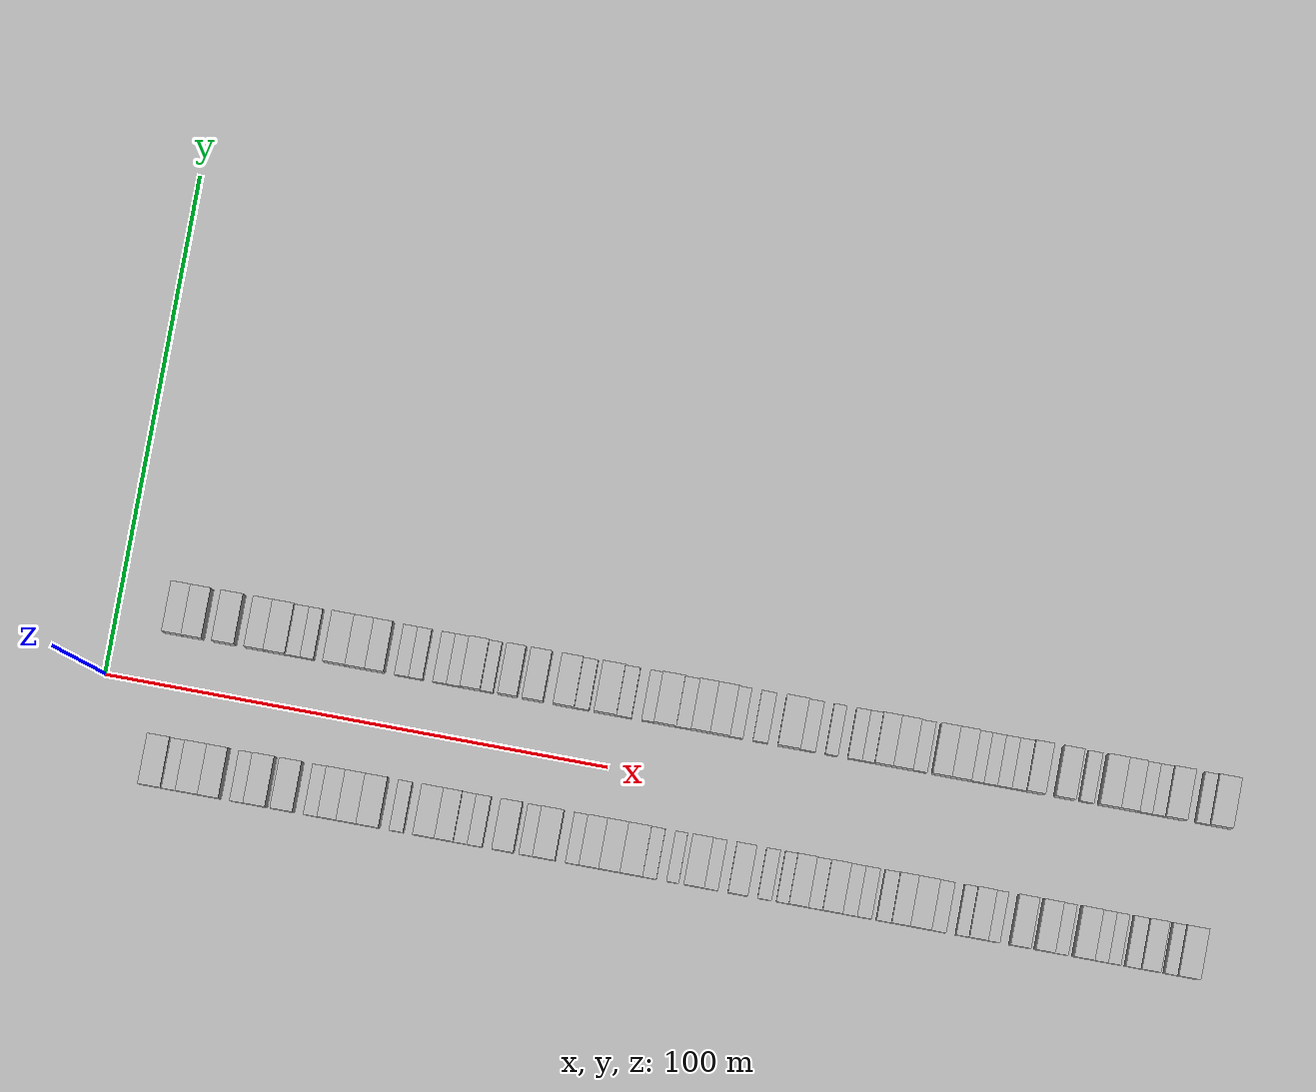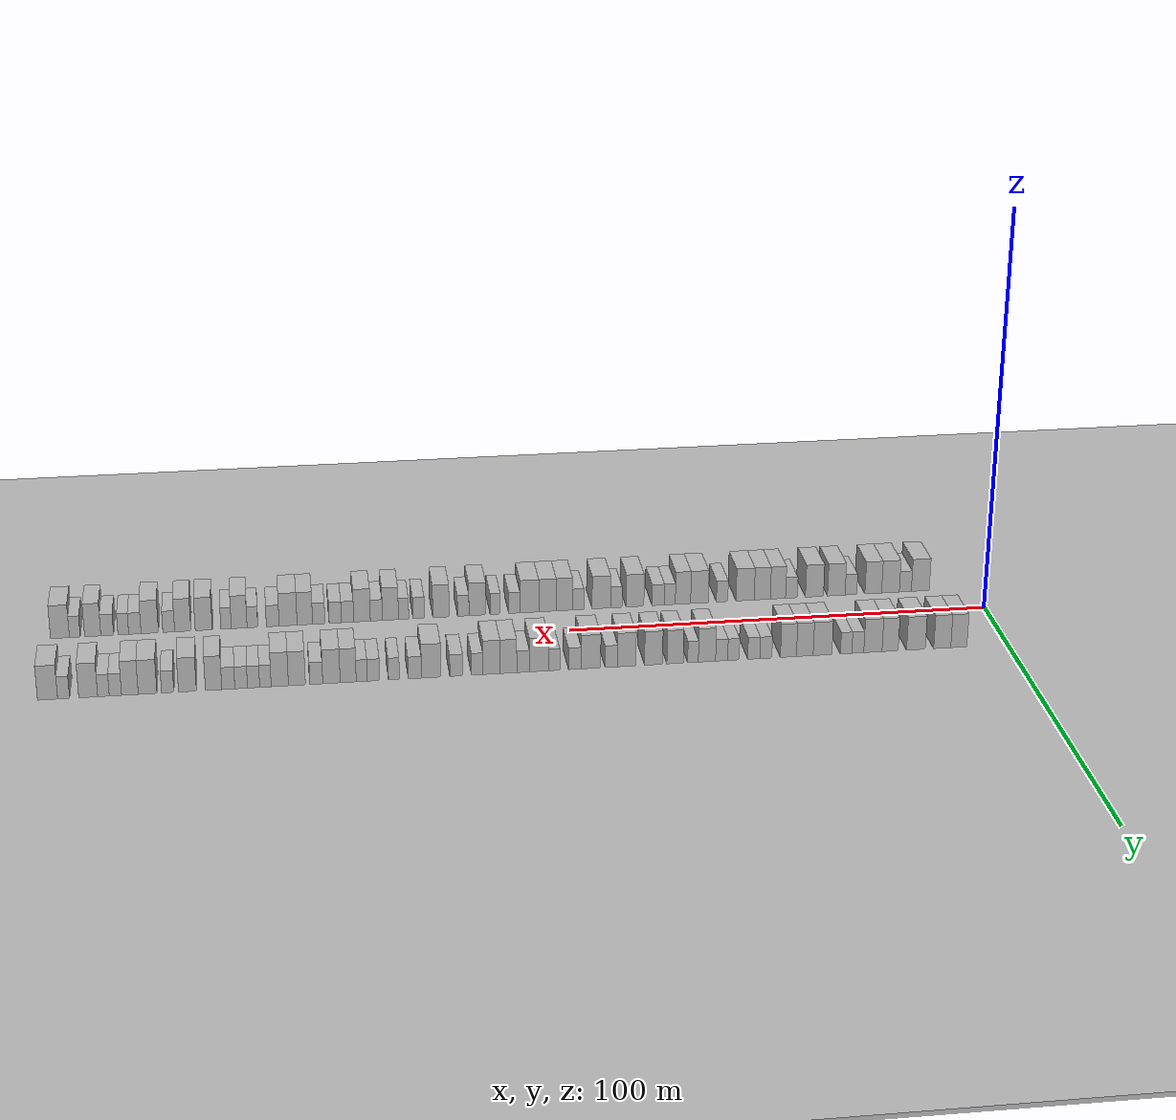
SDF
<?xml version="1.0" encoding="utf-8"?>

<sdf version="1.6">

   <world name="default">

      <gui fullscreen="0">

         <camera name="user_camera">

            <pose>-15 0 4.57585 0 0 0</pose>

            <view_controller>orbit</view_controller>

         </camera>

      </gui>

      <scene>

         <sky>

           <clouds>

             <speed>12</speed>

           </clouds>

         </sky>

         <ambient>0.4 0.4 0.4 1</ambient>

         <background>0.7 0.7 0.7 1</background>

         <shadows>1</shadows>

      </scene>

      <gravity>0 0 -9.8066</gravity>

      <magnetic_field>6e-06 2.3e-05 -4.2e-05</magnetic_field>

      <physics default="0" name="default_physics" type="ode">

         <ode>

            <solver>

               <type>quick</type>

               <iters>10</iters>

               <sor>1.0</sor>

               <use_dynamic_moi_rescaling>0</use_dynamic_moi_rescaling>

            </solver>

            <constraints>

               <cfm>0</cfm>

               <erp>0.2</erp>

               <contact_max_correcting_vel>100</contact_max_correcting_vel>

               <contact_surface_layer>0.001</contact_surface_layer>

            </constraints>

         </ode>

         <max_step_size>0.004</max_step_size>

         <real_time_factor>1</real_time_factor>

         <real_time_update_rate>250</real_time_update_rate>

      </physics>

      <light name="sun" type="directional">

         <cast_shadows>1</cast_shadows>

         <pose>0 0 10 0 0 0</pose>

         <diffuse>0.8 0.8 0.8 1</diffuse>

         <specular>0.2 0.2 0.2 1</specular>

         <attenuation>

            <range>1000</range>

            <constant>0.9</constant>

            <linear>0.01</linear>

            <quadratic>0.001</quadratic>

         </attenuation>

         <direction>-0.5 0.1 -0.9</direction>

      </light>

      <include>

         <name>ground_plane_1</name>

         <uri>model://HANNAS_ground_plane</uri>

         <pose>0 0 0  0 0 0</pose>

      </include>

      <include>

         <name>ground_plane_2</name>

         <uri>model://HANNAS_ground_plane</uri>

         <pose>100 0 0  0 0 0</pose>

      </include>

      <model name="building_1">

         <static>1</static>

         <pose frame="">11.9153 15.0000 0 0.000000 0.000000 1.570796</pose>

         <link name="link">

            <pose frame="">0 0 4.50 0 0 0</pose>

            <collision name="collision">

               <geometry>

                  <box>

                     <size>10.0000 3.8306 9.0000</size>

                  </box>

               </geometry>

               <max_contacts>10</max_contacts>

               <surface>

                  <contact>

                     <ode/>

                  </contact>

                  <bounce/>

                  <friction>

                     <torsional>

                        <ode/>

                     </torsional>

                     <ode/>

                  </friction>

               </surface>

            </collision>

            <visual name="visual">

               <cast_shadows>0</cast_shadows>

               <geometry>

                  <box>

                     <size>10.0000 3.8306 9.0000</size>

                  </box>

               </geometry>

               <material>

                  <script>

                     <uri>model://HANNAS_wall/materials/scripts</uri>

                     <uri>model://HANNAS_wall/materials/textures</uri>

                     <name>vrc/HANNAS_wall</name>

                  </script>

               </material>

            </visual>

            <self_collide>0</self_collide>

            <enable_wind>0</enable_wind>

            <kinematic>0</kinematic>

         </link>

      </model>

      <model name="building_2">

         <static>1</static>

         <pose frame="">15.8499 15.0000 0 0.000000 0.000000 1.570796</pose>

         <link name="link">

            <pose frame="">0 0 4.50 0 0 0</pose>

            <collision name="collision">

               <geometry>

                  <box>

                     <size>10.0000 4.0385 9.0000</size>

                  </box>

               </geometry>

               <max_contacts>10</max_contacts>

               <surface>

                  <contact>

                     <ode/>

                  </contact>

                  <bounce/>

                  <friction>

                     <torsional>

                        <ode/>

                     </torsional>

                     <ode/>

                  </friction>

               </surface>

            </collision>

            <visual name="visual">

               <cast_shadows>0</cast_shadows>

               <geometry>

                  <box>

                     <size>10.0000 4.0385 9.0000</size>

                  </box>

               </geometry>

               <material>

                  <script>

                     <uri>model://HANNAS_wall/materials/scripts</uri>

                     <uri>model://HANNAS_wall/materials/textures</uri>

                     <name>vrc/HANNAS_wall</name>

                  </script>

               </material>

            </visual>

            <self_collide>0</self_collide>

            <enable_wind>0</enable_wind>

            <kinematic>0</kinematic>

         </link>

      </model>

      <model name="building_3">

         <static>1</static>

         <pose frame="">22.0802 15.0000 0 0.000000 0.000000 1.570796</pose>

         <link name="link">

            <pose frame="">0 0 4.50 0 0 0</pose>

            <collision name="collision">

               <geometry>

                  <box>

                     <size>10.0000 4.4222 9.0000</size>

                  </box>

               </geometry>

               <max_contacts>10</max_contacts>

               <surface>

                  <contact>

                     <ode/>

                  </contact>

                  <bounce/>

                  <friction>

                     <torsional>

                        <ode/>

                     </torsional>

                     <ode/>

                  </friction>

               </surface>

            </collision>

            <visual name="visual">

               <cast_shadows>0</cast_shadows>

               <geometry>

                  <box>

                     <size>10.0000 4.4222 9.0000</size>

                  </box>

               </geometry>

               <material>

                  <script>

                     <uri>model://HANNAS_wall/materials/scripts</uri>

                     <uri>model://HANNAS_wall/materials/textures</uri>

                     <name>vrc/HANNAS_wall</name>

                  </script>

               </material>

            </visual>

            <self_collide>0</self_collide>

            <enable_wind>0</enable_wind>

            <kinematic>0</kinematic>

         </link>

      </model>

      <model name="building_4">

         <static>1</static>

         <pose frame="">28.1877 15.0000 0 0.000000 0.000000 1.570796</pose>

         <link name="link">

            <pose frame="">0 0 4.50 0 0 0</pose>

            <collision name="collision">

               <geometry>

                  <box>

                     <size>10.0000 3.7928 9.0000</size>

                  </box>

               </geometry>

               <max_contacts>10</max_contacts>

               <surface>

                  <contact>

                     <ode/>

                  </contact>

                  <bounce/>

                  <friction>

                     <torsional>

                        <ode/>

                     </torsional>

                     <ode/>

                  </friction>

               </surface>

            </collision>

            <visual name="visual">

               <cast_shadows>0</cast_shadows>

               <geometry>

                  <box>

                     <size>10.0000 3.7928 9.0000</size>

                  </box>

               </geometry>

               <material>

                  <script>

                     <uri>model://HANNAS_wall/materials/scripts</uri>

                     <uri>model://HANNAS_wall/materials/textures</uri>

                     <name>vrc/HANNAS_wall</name>

                  </script>

               </material>

            </visual>

            <self_collide>0</self_collide>

            <enable_wind>0</enable_wind>

            <kinematic>0</kinematic>

         </link>

      </model>

      <model name="building_5">

         <static>1</static>

         <pose frame="">32.2381 15.0000 0 0.000000 0.000000 1.570796</pose>

         <link name="link">

            <pose frame="">0 0 4.50 0 0 0</pose>

            <collision name="collision">

               <geometry>

                  <box>

                     <size>10.0000 4.3079 9.0000</size>

                  </box>

               </geometry>

               <max_contacts>10</max_contacts>

               <surface>

                  <contact>

                     <ode/>

                  </contact>

                  <bounce/>

                  <friction>

                     <torsional>

                        <ode/>

                     </torsional>

                     <ode/>

                  </friction>

               </surface>

            </collision>

            <visual name="visual">

               <cast_shadows>0</cast_shadows>

               <geometry>

                  <box>

                     <size>10.0000 4.3079 9.0000</size>

                  </box>

               </geometry>

               <material>

                  <script>

                     <uri>model://HANNAS_wall/materials/scripts</uri>

                     <uri>model://HANNAS_wall/materials/textures</uri>

                     <name>vrc/HANNAS_wall</name>

                  </script>

               </material>

            </visual>

            <self_collide>0</self_collide>

            <enable_wind>0</enable_wind>

            <kinematic>0</kinematic>

         </link>

      </model>

      <model name="building_6">

         <static>1</static>

         <pose frame="">35.7951 15.0000 0 0.000000 0.000000 1.570796</pose>

         <link name="link">

            <pose frame="">0 0 3.00 0 0 0</pose>

            <collision name="collision">

               <geometry>

                  <box>

                     <size>10.0000 2.8061 6.0000</size>

                  </box>

               </geometry>

               <max_contacts>10</max_contacts>

               <surface>

                  <contact>

                     <ode/>

                  </contact>

                  <bounce/>

                  <friction>

                     <torsional>

                        <ode/>

                     </torsional>

                     <ode/>

                  </friction>

               </surface>

            </collision>

            <visual name="visual">

               <cast_shadows>0</cast_shadows>

               <geometry>

                  <box>

                     <size>10.0000 2.8061 6.0000</size>

                  </box>

               </geometry>

               <material>

                  <script>

                     <uri>model://HANNAS_wall/materials/scripts</uri>

                     <uri>model://HANNAS_wall/materials/textures</uri>

                     <name>vrc/HANNAS_wall</name>

                  </script>

               </material>

            </visual>

            <self_collide>0</self_collide>

            <enable_wind>0</enable_wind>

            <kinematic>0</kinematic>

         </link>

      </model>

      <model name="building_7">

         <static>1</static>

         <pose frame="">38.5435 15.0000 0 0.000000 0.000000 1.570796</pose>

         <link name="link">

            <pose frame="">0 0 3.00 0 0 0</pose>

            <collision name="collision">

               <geometry>

                  <box>

                     <size>10.0000 2.6907 6.0000</size>

                  </box>

               </geometry>

               <max_contacts>10</max_contacts>

               <surface>

                  <contact>

                     <ode/>

                  </contact>

                  <bounce/>

                  <friction>

                     <torsional>

                        <ode/>

                     </torsional>

                     <ode/>

                  </friction>

               </surface>

            </collision>

            <visual name="visual">

               <cast_shadows>0</cast_shadows>

               <geometry>

                  <box>

                     <size>10.0000 2.6907 6.0000</size>

                  </box>

               </geometry>

               <material>

                  <script>

                     <uri>model://HANNAS_wall/materials/scripts</uri>

                     <uri>model://HANNAS_wall/materials/textures</uri>

                     <name>vrc/HANNAS_wall</name>

                  </script>

               </material>

            </visual>

            <self_collide>0</self_collide>

            <enable_wind>0</enable_wind>

            <kinematic>0</kinematic>

         </link>

      </model>

      <model name="building_8">

         <static>1</static>

         <pose frame="">44.0865 15.0000 0 0.000000 0.000000 1.570796</pose>

         <link name="link">

            <pose frame="">0 0 4.50 0 0 0</pose>

            <collision name="collision">

               <geometry>

                  <box>

                     <size>10.0000 4.3954 9.0000</size>

                  </box>

               </geometry>

               <max_contacts>10</max_contacts>

               <surface>

                  <contact>

                     <ode/>

                  </contact>

                  <bounce/>

                  <friction>

                     <torsional>

                        <ode/>

                     </torsional>

                     <ode/>

                  </friction>

               </surface>

            </collision>

            <visual name="visual">

               <cast_shadows>0</cast_shadows>

               <geometry>

                  <box>

                     <size>10.0000 4.3954 9.0000</size>

                  </box>

               </geometry>

               <material>

                  <script>

                     <uri>model://HANNAS_wall/materials/scripts</uri>

                     <uri>model://HANNAS_wall/materials/textures</uri>

                     <name>vrc/HANNAS_wall</name>

                  </script>

               </material>

            </visual>

            <self_collide>0</self_collide>

            <enable_wind>0</enable_wind>

            <kinematic>0</kinematic>

         </link>

      </model>

      <model name="building_9">

         <static>1</static>

         <pose frame="">48.2408 15.0000 0 0.000000 0.000000 1.570796</pose>

         <link name="link">

            <pose frame="">0 0 4.50 0 0 0</pose>

            <collision name="collision">

               <geometry>

                  <box>

                     <size>10.0000 3.9131 9.0000</size>

                  </box>

               </geometry>

               <max_contacts>10</max_contacts>

               <surface>

                  <contact>

                     <ode/>

                  </contact>

                  <bounce/>

                  <friction>

                     <torsional>

                        <ode/>

                     </torsional>

                     <ode/>

                  </friction>

               </surface>

            </collision>

            <visual name="visual">

               <cast_shadows>0</cast_shadows>

               <geometry>

                  <box>

                     <size>10.0000 3.9131 9.0000</size>

                  </box>

               </geometry>

               <material>

                  <script>

                     <uri>model://HANNAS_wall/materials/scripts</uri>

                     <uri>model://HANNAS_wall/materials/textures</uri>

                     <name>vrc/HANNAS_wall</name>

                  </script>

               </material>

            </visual>

            <self_collide>0</self_collide>

            <enable_wind>0</enable_wind>

            <kinematic>0</kinematic>

         </link>

      </model>

      <model name="building_10">

         <static>1</static>

         <pose frame="">52.0716 15.0000 0 0.000000 0.000000 1.570796</pose>

         <link name="link">

            <pose frame="">0 0 4.50 0 0 0</pose>

            <collision name="collision">

               <geometry>

                  <box>

                     <size>10.0000 3.7485 9.0000</size>

                  </box>

               </geometry>

               <max_contacts>10</max_contacts>

               <surface>

                  <contact>

                     <ode/>

                  </contact>

                  <bounce/>

                  <friction>

                     <torsional>

                        <ode/>

                     </torsional>

                     <ode/>

                  </friction>

               </surface>

            </collision>

            <visual name="visual">

               <cast_shadows>0</cast_shadows>

               <geometry>

                  <box>

                     <size>10.0000 3.7485 9.0000</size>

                  </box>

               </geometry>

               <material>

                  <script>

                     <uri>model://HANNAS_wall/materials/scripts</uri>

                     <uri>model://HANNAS_wall/materials/textures</uri>

                     <name>vrc/HANNAS_wall</name>

                  </script>

               </material>

            </visual>

            <self_collide>0</self_collide>

            <enable_wind>0</enable_wind>

            <kinematic>0</kinematic>

         </link>

      </model>

      <model name="building_11">

         <static>1</static>

         <pose frame="">57.3445 15.0000 0 0.000000 0.000000 1.570796</pose>

         <link name="link">

            <pose frame="">0 0 3.00 0 0 0</pose>

            <collision name="collision">

               <geometry>

                  <box>

                     <size>10.0000 2.7974 6.0000</size>

                  </box>

               </geometry>

               <max_contacts>10</max_contacts>

               <surface>

                  <contact>

                     <ode/>

                  </contact>

                  <bounce/>

                  <friction>

                     <torsional>

                        <ode/>

                     </torsional>

                     <ode/>

                  </friction>

               </surface>

            </collision>

            <visual name="visual">

               <cast_shadows>0</cast_shadows>

               <geometry>

                  <box>

                     <size>10.0000 2.7974 6.0000</size>

                  </box>

               </geometry>

               <material>

                  <script>

                     <uri>model://HANNAS_wall/materials/scripts</uri>

                     <uri>model://HANNAS_wall/materials/textures</uri>

                     <name>vrc/HANNAS_wall</name>

                  </script>

               </material>

            </visual>

            <self_collide>0</self_collide>

            <enable_wind>0</enable_wind>

            <kinematic>0</kinematic>

         </link>

      </model>

      <model name="building_12">

         <static>1</static>

         <pose frame="">60.1542 15.0000 0 0.000000 0.000000 1.570796</pose>

         <link name="link">

            <pose frame="">0 0 3.00 0 0 0</pose>

            <collision name="collision">

               <geometry>

                  <box>

                     <size>10.0000 2.8222 6.0000</size>

                  </box>

               </geometry>

               <max_contacts>10</max_contacts>

               <surface>

                  <contact>

                     <ode/>

                  </contact>

                  <bounce/>

                  <friction>

                     <torsional>

                        <ode/>

                     </torsional>

                     <ode/>

                  </friction>

               </surface>

            </collision>

            <visual name="visual">

               <cast_shadows>0</cast_shadows>

               <geometry>

                  <box>

                     <size>10.0000 2.8222 6.0000</size>

                  </box>

               </geometry>

               <material>

                  <script>

                     <uri>model://HANNAS_wall/materials/scripts</uri>

                     <uri>model://HANNAS_wall/materials/textures</uri>

                     <name>vrc/HANNAS_wall</name>

                  </script>

               </material>

            </visual>

            <self_collide>0</self_collide>

            <enable_wind>0</enable_wind>

            <kinematic>0</kinematic>

         </link>

      </model>

      <model name="building_13">

         <static>1</static>

         <pose frame="">64.9025 15.0000 0 0.000000 0.000000 1.570796</pose>

         <link name="link">

            <pose frame="">0 0 3.00 0 0 0</pose>

            <collision name="collision">

               <geometry>

                  <box>

                     <size>10.0000 2.6743 6.0000</size>

                  </box>

               </geometry>

               <max_contacts>10</max_contacts>

               <surface>

                  <contact>

                     <ode/>

                  </contact>

                  <bounce/>

                  <friction>

                     <torsional>

                        <ode/>

                     </torsional>

                     <ode/>

                  </friction>

               </surface>

            </collision>

            <visual name="visual">

               <cast_shadows>0</cast_shadows>

               <geometry>

                  <box>

                     <size>10.0000 2.6743 6.0000</size>

                  </box>

               </geometry>

               <material>

                  <script>

                     <uri>model://HANNAS_wall/materials/scripts</uri>

                     <uri>model://HANNAS_wall/materials/textures</uri>

                     <name>vrc/HANNAS_wall</name>

                  </script>

               </material>

            </visual>

            <self_collide>0</self_collide>

            <enable_wind>0</enable_wind>

            <kinematic>0</kinematic>

         </link>

      </model>

      <model name="building_14">

         <static>1</static>

         <pose frame="">67.6442 15.0000 0 0.000000 0.000000 1.570796</pose>

         <link name="link">

            <pose frame="">0 0 3.00 0 0 0</pose>

            <collision name="collision">

               <geometry>

                  <box>

                     <size>10.0000 2.8091 6.0000</size>

                  </box>

               </geometry>

               <max_contacts>10</max_contacts>

               <surface>

                  <contact>

                     <ode/>

                  </contact>

                  <bounce/>

                  <friction>

                     <torsional>

                        <ode/>

                     </torsional>

                     <ode/>

                  </friction>

               </surface>

            </collision>

            <visual name="visual">

               <cast_shadows>0</cast_shadows>

               <geometry>

                  <box>

                     <size>10.0000 2.8091 6.0000</size>

                  </box>

               </geometry>

               <material>

                  <script>

                     <uri>model://HANNAS_wall/materials/scripts</uri>

                     <uri>model://HANNAS_wall/materials/textures</uri>

                     <name>vrc/HANNAS_wall</name>

                  </script>

               </material>

            </visual>

            <self_collide>0</self_collide>

            <enable_wind>0</enable_wind>

            <kinematic>0</kinematic>

         </link>

      </model>

      <model name="building_15">

         <static>1</static>

         <pose frame="">71.0499 15.0000 0 0.000000 0.000000 1.570796</pose>

         <link name="link">

            <pose frame="">0 0 4.50 0 0 0</pose>

            <collision name="collision">

               <geometry>

                  <box>

                     <size>10.0000 4.0023 9.0000</size>

                  </box>

               </geometry>

               <max_contacts>10</max_contacts>

               <surface>

                  <contact>

                     <ode/>

                  </contact>

                  <bounce/>

                  <friction>

                     <torsional>

                        <ode/>

                     </torsional>

                     <ode/>

                  </friction>

               </surface>

            </collision>

            <visual name="visual">

               <cast_shadows>0</cast_shadows>

               <geometry>

                  <box>

                     <size>10.0000 4.0023 9.0000</size>

                  </box>

               </geometry>

               <material>

                  <script>

                     <uri>model://HANNAS_wall/materials/scripts</uri>

                     <uri>model://HANNAS_wall/materials/textures</uri>

                     <name>vrc/HANNAS_wall</name>

                  </script>

               </material>

            </visual>

            <self_collide>0</self_collide>

            <enable_wind>0</enable_wind>

            <kinematic>0</kinematic>

         </link>

      </model>

      <model name="building_16">

         <static>1</static>

         <pose frame="">74.2884 15.0000 0 0.000000 0.000000 1.570796</pose>

         <link name="link">

            <pose frame="">0 0 3.00 0 0 0</pose>

            <collision name="collision">

               <geometry>

                  <box>

                     <size>10.0000 2.4747 6.0000</size>

                  </box>

               </geometry>

               <max_contacts>10</max_contacts>

               <surface>

                  <contact>

                     <ode/>

                  </contact>

                  <bounce/>

                  <friction>

                     <torsional>

                        <ode/>

                     </torsional>

                     <ode/>

                  </friction>

               </surface>

            </collision>

            <visual name="visual">

               <cast_shadows>0</cast_shadows>

               <geometry>

                  <box>

                     <size>10.0000 2.4747 6.0000</size>

                  </box>

               </geometry>

               <material>

                  <script>

                     <uri>model://HANNAS_wall/materials/scripts</uri>

                     <uri>model://HANNAS_wall/materials/textures</uri>

                     <name>vrc/HANNAS_wall</name>

                  </script>

               </material>

            </visual>

            <self_collide>0</self_collide>

            <enable_wind>0</enable_wind>

            <kinematic>0</kinematic>

         </link>

      </model>

      <model name="building_17">

         <static>1</static>

         <pose frame="">78.4329 15.0000 0 0.000000 0.000000 1.570796</pose>

         <link name="link">

            <pose frame="">0 0 4.50 0 0 0</pose>

            <collision name="collision">

               <geometry>

                  <box>

                     <size>10.0000 3.8142 9.0000</size>

                  </box>

               </geometry>

               <max_contacts>10</max_contacts>

               <surface>

                  <contact>

                     <ode/>

                  </contact>

                  <bounce/>

                  <friction>

                     <torsional>

                        <ode/>

                     </torsional>

                     <ode/>

                  </friction>

               </surface>

            </collision>

            <visual name="visual">

               <cast_shadows>0</cast_shadows>

               <geometry>

                  <box>

                     <size>10.0000 3.8142 9.0000</size>

                  </box>

               </geometry>

               <material>

                  <script>

                     <uri>model://HANNAS_wall/materials/scripts</uri>

                     <uri>model://HANNAS_wall/materials/textures</uri>

                     <name>vrc/HANNAS_wall</name>

                  </script>

               </material>

            </visual>

            <self_collide>0</self_collide>

            <enable_wind>0</enable_wind>

            <kinematic>0</kinematic>

         </link>

      </model>

      <model name="building_18">

         <static>1</static>

         <pose frame="">83.4169 15.0000 0 0.000000 0.000000 1.570796</pose>

         <link name="link">

            <pose frame="">0 0 4.50 0 0 0</pose>

            <collision name="collision">

               <geometry>

                  <box>

                     <size>10.0000 4.1538 9.0000</size>

                  </box>

               </geometry>

               <max_contacts>10</max_contacts>

               <surface>

                  <contact>

                     <ode/>

                  </contact>

                  <bounce/>

                  <friction>

                     <torsional>

                        <ode/>

                     </torsional>

                     <ode/>

                  </friction>

               </surface>

            </collision>

            <visual name="visual">

               <cast_shadows>0</cast_shadows>

               <geometry>

                  <box>

                     <size>10.0000 4.1538 9.0000</size>

                  </box>

               </geometry>

               <material>

                  <script>

                     <uri>model://HANNAS_wall/materials/scripts</uri>

                     <uri>model://HANNAS_wall/materials/textures</uri>

                     <name>vrc/HANNAS_wall</name>

                  </script>

               </material>

            </visual>

            <self_collide>0</self_collide>

            <enable_wind>0</enable_wind>

            <kinematic>0</kinematic>

         </link>

      </model>

      <model name="building_19">

         <static>1</static>

         <pose frame="">89.5915 15.0000 0 0.000000 0.000000 1.570796</pose>

         <link name="link">

            <pose frame="">0 0 4.50 0 0 0</pose>

            <collision name="collision">

               <geometry>

                  <box>

                     <size>10.0000 4.1954 9.0000</size>

                  </box>

               </geometry>

               <max_contacts>10</max_contacts>

               <surface>

                  <contact>

                     <ode/>

                  </contact>

                  <bounce/>

                  <friction>

                     <torsional>

                        <ode/>

                     </torsional>

                     <ode/>

                  </friction>

               </surface>

            </collision>

            <visual name="visual">

               <cast_shadows>0</cast_shadows>

               <geometry>

                  <box>

                     <size>10.0000 4.1954 9.0000</size>

                  </box>

               </geometry>

               <material>

                  <script>

                     <uri>model://HANNAS_wall/materials/scripts</uri>

                     <uri>model://HANNAS_wall/materials/textures</uri>

                     <name>vrc/HANNAS_wall</name>

                  </script>

               </material>

            </visual>

            <self_collide>0</self_collide>

            <enable_wind>0</enable_wind>

            <kinematic>0</kinematic>

         </link>

      </model>

      <model name="building_20">

         <static>1</static>

         <pose frame="">93.1447 15.0000 0 0.000000 0.000000 1.570796</pose>

         <link name="link">

            <pose frame="">0 0 3.00 0 0 0</pose>

            <collision name="collision">

               <geometry>

                  <box>

                     <size>10.0000 2.9111 6.0000</size>

                  </box>

               </geometry>

               <max_contacts>10</max_contacts>

               <surface>

                  <contact>

                     <ode/>

                  </contact>

                  <bounce/>

                  <friction>

                     <torsional>

                        <ode/>

                     </torsional>

                     <ode/>

                  </friction>

               </surface>

            </collision>

            <visual name="visual">

               <cast_shadows>0</cast_shadows>

               <geometry>

                  <box>

                     <size>10.0000 2.9111 6.0000</size>

                  </box>

               </geometry>

               <material>

                  <script>

                     <uri>model://HANNAS_wall/materials/scripts</uri>

                     <uri>model://HANNAS_wall/materials/textures</uri>

                     <name>vrc/HANNAS_wall</name>

                  </script>

               </material>

            </visual>

            <self_collide>0</self_collide>

            <enable_wind>0</enable_wind>

            <kinematic>0</kinematic>

         </link>

      </model>

      <model name="building_21">

         <static>1</static>

         <pose frame="">97.8283 15.0000 0 0.000000 0.000000 1.570796</pose>

         <link name="link">

            <pose frame="">0 0 4.50 0 0 0</pose>

            <collision name="collision">

               <geometry>

                  <box>

                     <size>10.0000 4.4561 9.0000</size>

                  </box>

               </geometry>

               <max_contacts>10</max_contacts>

               <surface>

                  <contact>

                     <ode/>

                  </contact>

                  <bounce/>

                  <friction>

                     <torsional>

                        <ode/>

                     </torsional>

                     <ode/>

                  </friction>

               </surface>

            </collision>

            <visual name="visual">

               <cast_shadows>0</cast_shadows>

               <geometry>

                  <box>

                     <size>10.0000 4.4561 9.0000</size>

                  </box>

               </geometry>

               <material>

                  <script>

                     <uri>model://HANNAS_wall/materials/scripts</uri>

                     <uri>model://HANNAS_wall/materials/textures</uri>

                     <name>vrc/HANNAS_wall</name>

                  </script>

               </material>

            </visual>

            <self_collide>0</self_collide>

            <enable_wind>0</enable_wind>

            <kinematic>0</kinematic>

         </link>

      </model>

      <model name="building_22">

         <static>1</static>

         <pose frame="">101.5247 15.0000 0 0.000000 0.000000 1.570796</pose>

         <link name="link">

            <pose frame="">0 0 3.00 0 0 0</pose>

            <collision name="collision">

               <geometry>

                  <box>

                     <size>10.0000 2.9366 6.0000</size>

                  </box>

               </geometry>

               <max_contacts>10</max_contacts>

               <surface>

                  <contact>

                     <ode/>

                  </contact>

                  <bounce/>

                  <friction>

                     <torsional>

                        <ode/>

                     </torsional>

                     <ode/>

                  </friction>

               </surface>

            </collision>

            <visual name="visual">

               <cast_shadows>0</cast_shadows>

               <geometry>

                  <box>

                     <size>10.0000 2.9366 6.0000</size>

                  </box>

               </geometry>

               <material>

                  <script>

                     <uri>model://HANNAS_wall/materials/scripts</uri>

                     <uri>model://HANNAS_wall/materials/textures</uri>

                     <name>vrc/HANNAS_wall</name>

                  </script>

               </material>

            </visual>

            <self_collide>0</self_collide>

            <enable_wind>0</enable_wind>

            <kinematic>0</kinematic>

         </link>

      </model>

      <model name="building_23">

         <static>1</static>

         <pose frame="">106.2272 15.0000 0 0.000000 0.000000 1.570796</pose>

         <link name="link">

            <pose frame="">0 0 3.00 0 0 0</pose>

            <collision name="collision">

               <geometry>

                  <box>

                     <size>10.0000 2.4686 6.0000</size>

                  </box>

               </geometry>

               <max_contacts>10</max_contacts>

               <surface>

                  <contact>

                     <ode/>

                  </contact>

                  <bounce/>

                  <friction>

                     <torsional>

                        <ode/>

                     </torsional>

                     <ode/>

                  </friction>

               </surface>

            </collision>

            <visual name="visual">

               <cast_shadows>0</cast_shadows>

               <geometry>

                  <box>

                     <size>10.0000 2.4686 6.0000</size>

                  </box>

               </geometry>

               <material>

                  <script>

                     <uri>model://HANNAS_wall/materials/scripts</uri>

                     <uri>model://HANNAS_wall/materials/textures</uri>

                     <name>vrc/HANNAS_wall</name>

                  </script>

               </material>

            </visual>

            <self_collide>0</self_collide>

            <enable_wind>0</enable_wind>

            <kinematic>0</kinematic>

         </link>

      </model>

      <model name="building_24">

         <static>1</static>

         <pose frame="">109.6873 15.0000 0 0.000000 0.000000 1.570796</pose>

         <link name="link">

            <pose frame="">0 0 4.50 0 0 0</pose>

            <collision name="collision">

               <geometry>

                  <box>

                     <size>10.0000 4.4515 9.0000</size>

                  </box>

               </geometry>

               <max_contacts>10</max_contacts>

               <surface>

                  <contact>

                     <ode/>

                  </contact>

                  <bounce/>

                  <friction>

                     <torsional>

                        <ode/>

                     </torsional>

                     <ode/>

                  </friction>

               </surface>

            </collision>

            <visual name="visual">

               <cast_shadows>0</cast_shadows>

               <geometry>

                  <box>

                     <size>10.0000 4.4515 9.0000</size>

                  </box>

               </geometry>

               <material>

                  <script>

                     <uri>model://HANNAS_wall/materials/scripts</uri>

                     <uri>model://HANNAS_wall/materials/textures</uri>

                     <name>vrc/HANNAS_wall</name>

                  </script>

               </material>

            </visual>

            <self_collide>0</self_collide>

            <enable_wind>0</enable_wind>

            <kinematic>0</kinematic>

         </link>

      </model>

      <model name="building_25">

         <static>1</static>

         <pose frame="">113.3651 15.0000 0 0.000000 0.000000 1.570796</pose>

         <link name="link">

            <pose frame="">0 0 3.00 0 0 0</pose>

            <collision name="collision">

               <geometry>

                  <box>

                     <size>10.0000 2.9041 6.0000</size>

                  </box>

               </geometry>

               <max_contacts>10</max_contacts>

               <surface>

                  <contact>

                     <ode/>

                  </contact>

                  <bounce/>

                  <friction>

                     <torsional>

                        <ode/>

                     </torsional>

                     <ode/>

                  </friction>

               </surface>

            </collision>

            <visual name="visual">

               <cast_shadows>0</cast_shadows>

               <geometry>

                  <box>

                     <size>10.0000 2.9041 6.0000</size>

                  </box>

               </geometry>

               <material>

                  <script>

                     <uri>model://HANNAS_wall/materials/scripts</uri>

                     <uri>model://HANNAS_wall/materials/textures</uri>

                     <name>vrc/HANNAS_wall</name>

                  </script>

               </material>

            </visual>

            <self_collide>0</self_collide>

            <enable_wind>0</enable_wind>

            <kinematic>0</kinematic>

         </link>

      </model>

      <model name="building_26">

         <static>1</static>

         <pose frame="">116.7013 15.0000 0 0.000000 0.000000 1.570796</pose>

         <link name="link">

            <pose frame="">0 0 4.50 0 0 0</pose>

            <collision name="collision">

               <geometry>

                  <box>

                     <size>10.0000 3.7683 9.0000</size>

                  </box>

               </geometry>

               <max_contacts>10</max_contacts>

               <surface>

                  <contact>

                     <ode/>

                  </contact>

                  <bounce/>

                  <friction>

                     <torsional>

                        <ode/>

                     </torsional>

                     <ode/>

                  </friction>

               </surface>

            </collision>

            <visual name="visual">

               <cast_shadows>0</cast_shadows>

               <geometry>

                  <box>

                     <size>10.0000 3.7683 9.0000</size>

                  </box>

               </geometry>

               <material>

                  <script>

                     <uri>model://HANNAS_wall/materials/scripts</uri>

                     <uri>model://HANNAS_wall/materials/textures</uri>

                     <name>vrc/HANNAS_wall</name>

                  </script>

               </material>

            </visual>

            <self_collide>0</self_collide>

            <enable_wind>0</enable_wind>

            <kinematic>0</kinematic>

         </link>

      </model>

      <model name="building_27">

         <static>1</static>

         <pose frame="">120.5620 15.0000 0 0.000000 0.000000 1.570796</pose>

         <link name="link">

            <pose frame="">0 0 4.50 0 0 0</pose>

            <collision name="collision">

               <geometry>

                  <box>

                     <size>10.0000 3.9531 9.0000</size>

                  </box>

               </geometry>

               <max_contacts>10</max_contacts>

               <surface>

                  <contact>

                     <ode/>

                  </contact>

                  <bounce/>

                  <friction>

                     <torsional>

                        <ode/>

                     </torsional>

                     <ode/>

                  </friction>

               </surface>

            </collision>

            <visual name="visual">

               <cast_shadows>0</cast_shadows>

               <geometry>

                  <box>

                     <size>10.0000 3.9531 9.0000</size>

                  </box>

               </geometry>

               <material>

                  <script>

                     <uri>model://HANNAS_wall/materials/scripts</uri>

                     <uri>model://HANNAS_wall/materials/textures</uri>

                     <name>vrc/HANNAS_wall</name>

                  </script>

               </material>

            </visual>

            <self_collide>0</self_collide>

            <enable_wind>0</enable_wind>

            <kinematic>0</kinematic>

         </link>

      </model>

      <model name="building_28">

         <static>1</static>

         <pose frame="">123.8197 15.0000 0 0.000000 0.000000 1.570796</pose>

         <link name="link">

            <pose frame="">0 0 3.00 0 0 0</pose>

            <collision name="collision">

               <geometry>

                  <box>

                     <size>10.0000 2.5622 6.0000</size>

                  </box>

               </geometry>

               <max_contacts>10</max_contacts>

               <surface>

                  <contact>

                     <ode/>

                  </contact>

                  <bounce/>

                  <friction>

                     <torsional>

                        <ode/>

                     </torsional>

                     <ode/>

                  </friction>

               </surface>

            </collision>

            <visual name="visual">

               <cast_shadows>0</cast_shadows>

               <geometry>

                  <box>

                     <size>10.0000 2.5622 6.0000</size>

                  </box>

               </geometry>

               <material>

                  <script>

                     <uri>model://HANNAS_wall/materials/scripts</uri>

                     <uri>model://HANNAS_wall/materials/textures</uri>

                     <name>vrc/HANNAS_wall</name>

                  </script>

               </material>

            </visual>

            <self_collide>0</self_collide>

            <enable_wind>0</enable_wind>

            <kinematic>0</kinematic>

         </link>

      </model>

      <model name="building_29">

         <static>1</static>

         <pose frame="">128.5698 15.0000 0 0.000000 0.000000 1.570796</pose>

         <link name="link">

            <pose frame="">0 0 3.00 0 0 0</pose>

            <collision name="collision">

               <geometry>

                  <box>

                     <size>10.0000 2.9381 6.0000</size>

                  </box>

               </geometry>

               <max_contacts>10</max_contacts>

               <surface>

                  <contact>

                     <ode/>

                  </contact>

                  <bounce/>

                  <friction>

                     <torsional>

                        <ode/>

                     </torsional>

                     <ode/>

                  </friction>

               </surface>

            </collision>

            <visual name="visual">

               <cast_shadows>0</cast_shadows>

               <geometry>

                  <box>

                     <size>10.0000 2.9381 6.0000</size>

                  </box>

               </geometry>

               <material>

                  <script>

                     <uri>model://HANNAS_wall/materials/scripts</uri>

                     <uri>model://HANNAS_wall/materials/textures</uri>

                     <name>vrc/HANNAS_wall</name>

                  </script>

               </material>

            </visual>

            <self_collide>0</self_collide>

            <enable_wind>0</enable_wind>

            <kinematic>0</kinematic>

         </link>

      </model>

      <model name="building_30">

         <static>1</static>

         <pose frame="">134.2513 15.0000 0 0.000000 0.000000 1.570796</pose>

         <link name="link">

            <pose frame="">0 0 4.50 0 0 0</pose>

            <collision name="collision">

               <geometry>

                  <box>

                     <size>10.0000 4.4249 9.0000</size>

                  </box>

               </geometry>

               <max_contacts>10</max_contacts>

               <surface>

                  <contact>

                     <ode/>

                  </contact>

                  <bounce/>

                  <friction>

                     <torsional>

                        <ode/>

                     </torsional>

                     <ode/>

                  </friction>

               </surface>

            </collision>

            <visual name="visual">

               <cast_shadows>0</cast_shadows>

               <geometry>

                  <box>

                     <size>10.0000 4.4249 9.0000</size>

                  </box>

               </geometry>

               <material>

                  <script>

                     <uri>model://HANNAS_wall/materials/scripts</uri>

                     <uri>model://HANNAS_wall/materials/textures</uri>

                     <name>vrc/HANNAS_wall</name>

                  </script>

               </material>

            </visual>

            <self_collide>0</self_collide>

            <enable_wind>0</enable_wind>

            <kinematic>0</kinematic>

         </link>

      </model>

      <model name="building_31">

         <static>1</static>

         <pose frame="">137.9628 15.0000 0 0.000000 0.000000 1.570796</pose>

         <link name="link">

            <pose frame="">0 0 3.00 0 0 0</pose>

            <collision name="collision">

               <geometry>

                  <box>

                     <size>10.0000 2.9982 6.0000</size>

                  </box>

               </geometry>

               <max_contacts>10</max_contacts>

               <surface>

                  <contact>

                     <ode/>

                  </contact>

                  <bounce/>

                  <friction>

                     <torsional>

                        <ode/>

                     </torsional>

                     <ode/>

                  </friction>

               </surface>

            </collision>

            <visual name="visual">

               <cast_shadows>0</cast_shadows>

               <geometry>

                  <box>

                     <size>10.0000 2.9982 6.0000</size>

                  </box>

               </geometry>

               <material>

                  <script>

                     <uri>model://HANNAS_wall/materials/scripts</uri>

                     <uri>model://HANNAS_wall/materials/textures</uri>

                     <name>vrc/HANNAS_wall</name>

                  </script>

               </material>

            </visual>

            <self_collide>0</self_collide>

            <enable_wind>0</enable_wind>

            <kinematic>0</kinematic>

         </link>

      </model>

      <model name="building_32">

         <static>1</static>

         <pose frame="">142.6912 15.0000 0 0.000000 0.000000 1.570796</pose>

         <link name="link">

            <pose frame="">0 0 3.00 0 0 0</pose>

            <collision name="collision">

               <geometry>

                  <box>

                     <size>10.0000 2.4584 6.0000</size>

                  </box>

               </geometry>

               <max_contacts>10</max_contacts>

               <surface>

                  <contact>

                     <ode/>

                  </contact>

                  <bounce/>

                  <friction>

                     <torsional>

                        <ode/>

                     </torsional>

                     <ode/>

                  </friction>

               </surface>

            </collision>

            <visual name="visual">

               <cast_shadows>0</cast_shadows>

               <geometry>

                  <box>

                     <size>10.0000 2.4584 6.0000</size>

                  </box>

               </geometry>

               <material>

                  <script>

                     <uri>model://HANNAS_wall/materials/scripts</uri>

                     <uri>model://HANNAS_wall/materials/textures</uri>

                     <name>vrc/HANNAS_wall</name>

                  </script>

               </material>

            </visual>

            <self_collide>0</self_collide>

            <enable_wind>0</enable_wind>

            <kinematic>0</kinematic>

         </link>

      </model>

      <model name="building_33">

         <static>1</static>

         <pose frame="">147.3103 15.0000 0 0.000000 0.000000 1.570796</pose>

         <link name="link">

            <pose frame="">0 0 3.00 0 0 0</pose>

            <collision name="collision">

               <geometry>

                  <box>

                     <size>10.0000 2.7798 6.0000</size>

                  </box>

               </geometry>

               <max_contacts>10</max_contacts>

               <surface>

                  <contact>

                     <ode/>

                  </contact>

                  <bounce/>

                  <friction>

                     <torsional>

                        <ode/>

                     </torsional>

                     <ode/>

                  </friction>

               </surface>

            </collision>

            <visual name="visual">

               <cast_shadows>0</cast_shadows>

               <geometry>

                  <box>

                     <size>10.0000 2.7798 6.0000</size>

                  </box>

               </geometry>

               <material>

                  <script>

                     <uri>model://HANNAS_wall/materials/scripts</uri>

                     <uri>model://HANNAS_wall/materials/textures</uri>

                     <name>vrc/HANNAS_wall</name>

                  </script>

               </material>

            </visual>

            <self_collide>0</self_collide>

            <enable_wind>0</enable_wind>

            <kinematic>0</kinematic>

         </link>

      </model>

      <model name="building_34">

         <static>1</static>

         <pose frame="">149.9504 15.0000 0 0.000000 0.000000 1.570796</pose>

         <link name="link">

            <pose frame="">0 0 3.00 0 0 0</pose>

            <collision name="collision">

               <geometry>

                  <box>

                     <size>10.0000 2.5005 6.0000</size>

                  </box>

               </geometry>

               <max_contacts>10</max_contacts>

               <surface>

                  <contact>

                     <ode/>

                  </contact>

                  <bounce/>

                  <friction>

                     <torsional>

                        <ode/>

                     </torsional>

                     <ode/>

                  </friction>

               </surface>

            </collision>

            <visual name="visual">

               <cast_shadows>0</cast_shadows>

               <geometry>

                  <box>

                     <size>10.0000 2.5005 6.0000</size>

                  </box>

               </geometry>

               <material>

                  <script>

                     <uri>model://HANNAS_wall/materials/scripts</uri>

                     <uri>model://HANNAS_wall/materials/textures</uri>

                     <name>vrc/HANNAS_wall</name>

                  </script>

               </material>

            </visual>

            <self_collide>0</self_collide>

            <enable_wind>0</enable_wind>

            <kinematic>0</kinematic>

         </link>

      </model>

      <model name="building_35">

         <static>1</static>

         <pose frame="">153.0064 15.0000 0 0.000000 0.000000 1.570796</pose>

         <link name="link">

            <pose frame="">0 0 4.50 0 0 0</pose>

            <collision name="collision">

               <geometry>

                  <box>

                     <size>10.0000 3.6116 9.0000</size>

                  </box>

               </geometry>

               <max_contacts>10</max_contacts>

               <surface>

                  <contact>

                     <ode/>

                  </contact>

                  <bounce/>

                  <friction>

                     <torsional>

                        <ode/>

                     </torsional>

                     <ode/>

                  </friction>

               </surface>

            </collision>

            <visual name="visual">

               <cast_shadows>0</cast_shadows>

               <geometry>

                  <box>

                     <size>10.0000 3.6116 9.0000</size>

                  </box>

               </geometry>

               <material>

                  <script>

                     <uri>model://HANNAS_wall/materials/scripts</uri>

                     <uri>model://HANNAS_wall/materials/textures</uri>

                     <name>vrc/HANNAS_wall</name>

                  </script>

               </material>

            </visual>

            <self_collide>0</self_collide>

            <enable_wind>0</enable_wind>

            <kinematic>0</kinematic>

         </link>

      </model>

      <model name="building_36">

         <static>1</static>

         <pose frame="">156.7667 15.0000 0 0.000000 0.000000 1.570796</pose>

         <link name="link">

            <pose frame="">0 0 4.50 0 0 0</pose>

            <collision name="collision">

               <geometry>

                  <box>

                     <size>10.0000 3.9090 9.0000</size>

                  </box>

               </geometry>

               <max_contacts>10</max_contacts>

               <surface>

                  <contact>

                     <ode/>

                  </contact>

                  <bounce/>

                  <friction>

                     <torsional>

                        <ode/>

                     </torsional>

                     <ode/>

                  </friction>

               </surface>

            </collision>

            <visual name="visual">

               <cast_shadows>0</cast_shadows>

               <geometry>

                  <box>

                     <size>10.0000 3.9090 9.0000</size>

                  </box>

               </geometry>

               <material>

                  <script>

                     <uri>model://HANNAS_wall/materials/scripts</uri>

                     <uri>model://HANNAS_wall/materials/textures</uri>

                     <name>vrc/HANNAS_wall</name>

                  </script>

               </material>

            </visual>

            <self_collide>0</self_collide>

            <enable_wind>0</enable_wind>

            <kinematic>0</kinematic>

         </link>

      </model>

      <model name="building_37">

         <static>1</static>

         <pose frame="">160.1663 15.0000 0 0.000000 0.000000 1.570796</pose>

         <link name="link">

            <pose frame="">0 0 3.00 0 0 0</pose>

            <collision name="collision">

               <geometry>

                  <box>

                     <size>10.0000 2.8902 6.0000</size>

                  </box>

               </geometry>

               <max_contacts>10</max_contacts>

               <surface>

                  <contact>

                     <ode/>

                  </contact>

                  <bounce/>

                  <friction>

                     <torsional>

                        <ode/>

                     </torsional>

                     <ode/>

                  </friction>

               </surface>

            </collision>

            <visual name="visual">

               <cast_shadows>0</cast_shadows>

               <geometry>

                  <box>

                     <size>10.0000 2.8902 6.0000</size>

                  </box>

               </geometry>

               <material>

                  <script>

                     <uri>model://HANNAS_wall/materials/scripts</uri>

                     <uri>model://HANNAS_wall/materials/textures</uri>

                     <name>vrc/HANNAS_wall</name>

                  </script>

               </material>

            </visual>

            <self_collide>0</self_collide>

            <enable_wind>0</enable_wind>

            <kinematic>0</kinematic>

         </link>

      </model>

      <model name="building_38">

         <static>1</static>

         <pose frame="">164.5105 15.0000 0 0.000000 0.000000 1.570796</pose>

         <link name="link">

            <pose frame="">0 0 4.50 0 0 0</pose>

            <collision name="collision">

               <geometry>

                  <box>

                     <size>10.0000 3.7983 9.0000</size>

                  </box>

               </geometry>

               <max_contacts>10</max_contacts>

               <surface>

                  <contact>

                     <ode/>

                  </contact>

                  <bounce/>

                  <friction>

                     <torsional>

                        <ode/>

                     </torsional>

                     <ode/>

                  </friction>

               </surface>

            </collision>

            <visual name="visual">

               <cast_shadows>0</cast_shadows>

               <geometry>

                  <box>

                     <size>10.0000 3.7983 9.0000</size>

                  </box>

               </geometry>

               <material>

                  <script>

                     <uri>model://HANNAS_wall/materials/scripts</uri>

                     <uri>model://HANNAS_wall/materials/textures</uri>

                     <name>vrc/HANNAS_wall</name>

                  </script>

               </material>

            </visual>

            <self_collide>0</self_collide>

            <enable_wind>0</enable_wind>

            <kinematic>0</kinematic>

         </link>

      </model>

      <model name="building_39">

         <static>1</static>

         <pose frame="">168.3373 15.0000 0 0.000000 0.000000 1.570796</pose>

         <link name="link">

            <pose frame="">0 0 4.50 0 0 0</pose>

            <collision name="collision">

               <geometry>

                  <box>

                     <size>10.0000 3.8554 9.0000</size>

                  </box>

               </geometry>

               <max_contacts>10</max_contacts>

               <surface>

                  <contact>

                     <ode/>

                  </contact>

                  <bounce/>

                  <friction>

                     <torsional>

                        <ode/>

                     </torsional>

                     <ode/>

                  </friction>

               </surface>

            </collision>

            <visual name="visual">

               <cast_shadows>0</cast_shadows>

               <geometry>

                  <box>

                     <size>10.0000 3.8554 9.0000</size>

                  </box>

               </geometry>

               <material>

                  <script>

                     <uri>model://HANNAS_wall/materials/scripts</uri>

                     <uri>model://HANNAS_wall/materials/textures</uri>

                     <name>vrc/HANNAS_wall</name>

                  </script>

               </material>

            </visual>

            <self_collide>0</self_collide>

            <enable_wind>0</enable_wind>

            <kinematic>0</kinematic>

         </link>

      </model>

      <model name="building_40">

         <static>1</static>

         <pose frame="">171.5442 15.0000 0 0.000000 0.000000 1.570796</pose>

         <link name="link">

            <pose frame="">0 0 3.00 0 0 0</pose>

            <collision name="collision">

               <geometry>

                  <box>

                     <size>10.0000 2.5584 6.0000</size>

                  </box>

               </geometry>

               <max_contacts>10</max_contacts>

               <surface>

                  <contact>

                     <ode/>

                  </contact>

                  <bounce/>

                  <friction>

                     <torsional>

                        <ode/>

                     </torsional>

                     <ode/>

                  </friction>

               </surface>

            </collision>

            <visual name="visual">

               <cast_shadows>0</cast_shadows>

               <geometry>

                  <box>

                     <size>10.0000 2.5584 6.0000</size>

                  </box>

               </geometry>

               <material>

                  <script>

                     <uri>model://HANNAS_wall/materials/scripts</uri>

                     <uri>model://HANNAS_wall/materials/textures</uri>

                     <name>vrc/HANNAS_wall</name>

                  </script>

               </material>

            </visual>

            <self_collide>0</self_collide>

            <enable_wind>0</enable_wind>

            <kinematic>0</kinematic>

         </link>

      </model>

      <model name="building_41">

         <static>1</static>

         <pose frame="">174.1778 15.0000 0 0.000000 0.000000 1.570796</pose>

         <link name="link">

            <pose frame="">0 0 3.00 0 0 0</pose>

            <collision name="collision">

               <geometry>

                  <box>

                     <size>10.0000 2.7087 6.0000</size>

                  </box>

               </geometry>

               <max_contacts>10</max_contacts>

               <surface>

                  <contact>

                     <ode/>

                  </contact>

                  <bounce/>

                  <friction>

                     <torsional>

                        <ode/>

                     </torsional>

                     <ode/>

                  </friction>

               </surface>

            </collision>

            <visual name="visual">

               <cast_shadows>0</cast_shadows>

               <geometry>

                  <box>

                     <size>10.0000 2.7087 6.0000</size>

                  </box>

               </geometry>

               <material>

                  <script>

                     <uri>model://HANNAS_wall/materials/scripts</uri>

                     <uri>model://HANNAS_wall/materials/textures</uri>

                     <name>vrc/HANNAS_wall</name>

                  </script>

               </material>

            </visual>

            <self_collide>0</self_collide>

            <enable_wind>0</enable_wind>

            <kinematic>0</kinematic>

         </link>

      </model>

      <model name="building_42">

         <static>1</static>

         <pose frame="">176.9479 15.0000 0 0.000000 0.000000 1.570796</pose>

         <link name="link">

            <pose frame="">0 0 3.00 0 0 0</pose>

            <collision name="collision">

               <geometry>

                  <box>

                     <size>10.0000 2.8315 6.0000</size>

                  </box>

               </geometry>

               <max_contacts>10</max_contacts>

               <surface>

                  <contact>

                     <ode/>

                  </contact>

                  <bounce/>

                  <friction>

                     <torsional>

                        <ode/>

                     </torsional>

                     <ode/>

                  </friction>

               </surface>

            </collision>

            <visual name="visual">

               <cast_shadows>0</cast_shadows>

               <geometry>

                  <box>

                     <size>10.0000 2.8315 6.0000</size>

                  </box>

               </geometry>

               <material>

                  <script>

                     <uri>model://HANNAS_wall/materials/scripts</uri>

                     <uri>model://HANNAS_wall/materials/textures</uri>

                     <name>vrc/HANNAS_wall</name>

                  </script>

               </material>

            </visual>

            <self_collide>0</self_collide>

            <enable_wind>0</enable_wind>

            <kinematic>0</kinematic>

         </link>

      </model>

      <model name="building_43">

         <static>1</static>

         <pose frame="">179.8066 15.0000 0 0.000000 0.000000 1.570796</pose>

         <link name="link">

            <pose frame="">0 0 3.00 0 0 0</pose>

            <collision name="collision">

               <geometry>

                  <box>

                     <size>10.0000 2.8860 6.0000</size>

                  </box>

               </geometry>

               <max_contacts>10</max_contacts>

               <surface>

                  <contact>

                     <ode/>

                  </contact>

                  <bounce/>

                  <friction>

                     <torsional>

                        <ode/>

                     </torsional>

                     <ode/>

                  </friction>

               </surface>

            </collision>

            <visual name="visual">

               <cast_shadows>0</cast_shadows>

               <geometry>

                  <box>

                     <size>10.0000 2.8860 6.0000</size>

                  </box>

               </geometry>

               <material>

                  <script>

                     <uri>model://HANNAS_wall/materials/scripts</uri>

                     <uri>model://HANNAS_wall/materials/textures</uri>

                     <name>vrc/HANNAS_wall</name>

                  </script>

               </material>

            </visual>

            <self_collide>0</self_collide>

            <enable_wind>0</enable_wind>

            <kinematic>0</kinematic>

         </link>

      </model>

      <model name="building_44">

         <static>1</static>

         <pose frame="">183.0724 15.0000 0 0.000000 0.000000 1.570796</pose>

         <link name="link">

            <pose frame="">0 0 4.50 0 0 0</pose>

            <collision name="collision">

               <geometry>

                  <box>

                     <size>10.0000 3.6456 9.0000</size>

                  </box>

               </geometry>

               <max_contacts>10</max_contacts>

               <surface>

                  <contact>

                     <ode/>

                  </contact>

                  <bounce/>

                  <friction>

                     <torsional>

                        <ode/>

                     </torsional>

                     <ode/>

                  </friction>

               </surface>

            </collision>

            <visual name="visual">

               <cast_shadows>0</cast_shadows>

               <geometry>

                  <box>

                     <size>10.0000 3.6456 9.0000</size>

                  </box>

               </geometry>

               <material>

                  <script>

                     <uri>model://HANNAS_wall/materials/scripts</uri>

                     <uri>model://HANNAS_wall/materials/textures</uri>

                     <name>vrc/HANNAS_wall</name>

                  </script>

               </material>

            </visual>

            <self_collide>0</self_collide>

            <enable_wind>0</enable_wind>

            <kinematic>0</kinematic>

         </link>

      </model>

      <model name="building_45">

         <static>1</static>

         <pose frame="">188.8882 15.0000 0 0.000000 0.000000 1.570796</pose>

         <link name="link">

            <pose frame="">0 0 4.50 0 0 0</pose>

            <collision name="collision">

               <geometry>

                  <box>

                     <size>10.0000 3.9860 9.0000</size>

                  </box>

               </geometry>

               <max_contacts>10</max_contacts>

               <surface>

                  <contact>

                     <ode/>

                  </contact>

                  <bounce/>

                  <friction>

                     <torsional>

                        <ode/>

                     </torsional>

                     <ode/>

                  </friction>

               </surface>

            </collision>

            <visual name="visual">

               <cast_shadows>0</cast_shadows>

               <geometry>

                  <box>

                     <size>10.0000 3.9860 9.0000</size>

                  </box>

               </geometry>

               <material>

                  <script>

                     <uri>model://HANNAS_wall/materials/scripts</uri>

                     <uri>model://HANNAS_wall/materials/textures</uri>

                     <name>vrc/HANNAS_wall</name>

                  </script>

               </material>

            </visual>

            <self_collide>0</self_collide>

            <enable_wind>0</enable_wind>

            <kinematic>0</kinematic>

         </link>

      </model>

      <model name="building_46">

         <static>1</static>

         <pose frame="">193.2553 15.0000 0 0.000000 0.000000 1.570796</pose>

         <link name="link">

            <pose frame="">0 0 3.00 0 0 0</pose>

            <collision name="collision">

               <geometry>

                  <box>

                     <size>10.0000 2.7483 6.0000</size>

                  </box>

               </geometry>

               <max_contacts>10</max_contacts>

               <surface>

                  <contact>

                     <ode/>

                  </contact>

                  <bounce/>

                  <friction>

                     <torsional>

                        <ode/>

                     </torsional>

                     <ode/>

                  </friction>

               </surface>

            </collision>

            <visual name="visual">

               <cast_shadows>0</cast_shadows>

               <geometry>

                  <box>

                     <size>10.0000 2.7483 6.0000</size>

                  </box>

               </geometry>

               <material>

                  <script>

                     <uri>model://HANNAS_wall/materials/scripts</uri>

                     <uri>model://HANNAS_wall/materials/textures</uri>

                     <name>vrc/HANNAS_wall</name>

                  </script>

               </material>

            </visual>

            <self_collide>0</self_collide>

            <enable_wind>0</enable_wind>

            <kinematic>0</kinematic>

         </link>

      </model>

      <model name="building_47">

         <static>1</static>

         <pose frame="">197.7018 15.0000 0 0.000000 0.000000 1.570796</pose>

         <link name="link">

            <pose frame="">0 0 4.50 0 0 0</pose>

            <collision name="collision">

               <geometry>

                  <box>

                     <size>10.0000 4.1447 9.0000</size>

                  </box>

               </geometry>

               <max_contacts>10</max_contacts>

               <surface>

                  <contact>

                     <ode/>

                  </contact>

                  <bounce/>

                  <friction>

                     <torsional>

                        <ode/>

                     </torsional>

                     <ode/>

                  </friction>

               </surface>

            </collision>

            <visual name="visual">

               <cast_shadows>0</cast_shadows>

               <geometry>

                  <box>

                     <size>10.0000 4.1447 9.0000</size>

                  </box>

               </geometry>

               <material>

                  <script>

                     <uri>model://HANNAS_wall/materials/scripts</uri>

                     <uri>model://HANNAS_wall/materials/textures</uri>

                     <name>vrc/HANNAS_wall</name>

                  </script>

               </material>

            </visual>

            <self_collide>0</self_collide>

            <enable_wind>0</enable_wind>

            <kinematic>0</kinematic>

         </link>

      </model>

      <model name="building_48">

         <static>1</static>

         <pose frame="">201.6112 15.0000 0 0.000000 0.000000 1.570796</pose>

         <link name="link">

            <pose frame="">0 0 4.50 0 0 0</pose>

            <collision name="collision">

               <geometry>

                  <box>

                     <size>10.0000 3.6740 9.0000</size>

                  </box>

               </geometry>

               <max_contacts>10</max_contacts>

               <surface>

                  <contact>

                     <ode/>

                  </contact>

                  <bounce/>

                  <friction>

                     <torsional>

                        <ode/>

                     </torsional>

                     <ode/>

                  </friction>

               </surface>

            </collision>

            <visual name="visual">

               <cast_shadows>0</cast_shadows>

               <geometry>

                  <box>

                     <size>10.0000 3.6740 9.0000</size>

                  </box>

               </geometry>

               <material>

                  <script>

                     <uri>model://HANNAS_wall/materials/scripts</uri>

                     <uri>model://HANNAS_wall/materials/textures</uri>

                     <name>vrc/HANNAS_wall</name>

                  </script>

               </material>

            </visual>

            <self_collide>0</self_collide>

            <enable_wind>0</enable_wind>

            <kinematic>0</kinematic>

         </link>

      </model>

      <model name="building_49">

         <static>1</static>

         <pose frame="">204.8056 15.0000 0 0.000000 0.000000 1.570796</pose>

         <link name="link">

            <pose frame="">0 0 3.00 0 0 0</pose>

            <collision name="collision">

               <geometry>

                  <box>

                     <size>10.0000 2.7148 6.0000</size>

                  </box>

               </geometry>

               <max_contacts>10</max_contacts>

               <surface>

                  <contact>

                     <ode/>

                  </contact>

                  <bounce/>

                  <friction>

                     <torsional>

                        <ode/>

                     </torsional>

                     <ode/>

                  </friction>

               </surface>

            </collision>

            <visual name="visual">

               <cast_shadows>0</cast_shadows>

               <geometry>

                  <box>

                     <size>10.0000 2.7148 6.0000</size>

                  </box>

               </geometry>

               <material>

                  <script>

                     <uri>model://HANNAS_wall/materials/scripts</uri>

                     <uri>model://HANNAS_wall/materials/textures</uri>

                     <name>vrc/HANNAS_wall</name>

                  </script>

               </material>

            </visual>

            <self_collide>0</self_collide>

            <enable_wind>0</enable_wind>

            <kinematic>0</kinematic>

         </link>

      </model>

      <model name="building_50">

         <static>1</static>

         <pose frame="">207.4383 15.0000 0 0.000000 0.000000 1.570796</pose>

         <link name="link">

            <pose frame="">0 0 3.00 0 0 0</pose>

            <collision name="collision">

               <geometry>

                  <box>

                     <size>10.0000 2.5505 6.0000</size>

                  </box>

               </geometry>

               <max_contacts>10</max_contacts>

               <surface>

                  <contact>

                     <ode/>

                  </contact>

                  <bounce/>

                  <friction>

                     <torsional>

                        <ode/>

                     </torsional>

                     <ode/>

                  </friction>

               </surface>

            </collision>

            <visual name="visual">

               <cast_shadows>0</cast_shadows>

               <geometry>

                  <box>

                     <size>10.0000 2.5505 6.0000</size>

                  </box>

               </geometry>

               <material>

                  <script>

                     <uri>model://HANNAS_wall/materials/scripts</uri>

                     <uri>model://HANNAS_wall/materials/textures</uri>

                     <name>vrc/HANNAS_wall</name>

                  </script>

               </material>

            </visual>

            <self_collide>0</self_collide>

            <enable_wind>0</enable_wind>

            <kinematic>0</kinematic>

         </link>

      </model>

      <model name="building_51">

         <static>1</static>

         <pose frame="">210.7949 15.0000 0 0.000000 0.000000 1.570796</pose>

         <link name="link">

            <pose frame="">0 0 4.50 0 0 0</pose>

            <collision name="collision">

               <geometry>

                  <box>

                     <size>10.0000 4.1627 9.0000</size>

                  </box>

               </geometry>

               <max_contacts>10</max_contacts>

               <surface>

                  <contact>

                     <ode/>

                  </contact>

                  <bounce/>

                  <friction>

                     <torsional>

                        <ode/>

                     </torsional>

                     <ode/>

                  </friction>

               </surface>

            </collision>

            <visual name="visual">

               <cast_shadows>0</cast_shadows>

               <geometry>

                  <box>

                     <size>10.0000 4.1627 9.0000</size>

                  </box>

               </geometry>

               <material>

                  <script>

                     <uri>model://HANNAS_wall/materials/scripts</uri>

                     <uri>model://HANNAS_wall/materials/textures</uri>

                     <name>vrc/HANNAS_wall</name>

                  </script>

               </material>

            </visual>

            <self_collide>0</self_collide>

            <enable_wind>0</enable_wind>

            <kinematic>0</kinematic>

         </link>

      </model>

      <model name="building_52">

         <static>1</static>

         <pose frame="">216.1928 15.0000 0 0.000000 0.000000 1.570796</pose>

         <link name="link">

            <pose frame="">0 0 3.00 0 0 0</pose>

            <collision name="collision">

               <geometry>

                  <box>

                     <size>10.0000 2.6331 6.0000</size>

                  </box>

               </geometry>

               <max_contacts>10</max_contacts>

               <surface>

                  <contact>

                     <ode/>

                  </contact>

                  <bounce/>

                  <friction>

                     <torsional>

                        <ode/>

                     </torsional>

                     <ode/>

                  </friction>

               </surface>

            </collision>

            <visual name="visual">

               <cast_shadows>0</cast_shadows>

               <geometry>

                  <box>

                     <size>10.0000 2.6331 6.0000</size>

                  </box>

               </geometry>

               <material>

                  <script>

                     <uri>model://HANNAS_wall/materials/scripts</uri>

                     <uri>model://HANNAS_wall/materials/textures</uri>

                     <name>vrc/HANNAS_wall</name>

                  </script>

               </material>

            </visual>

            <self_collide>0</self_collide>

            <enable_wind>0</enable_wind>

            <kinematic>0</kinematic>

         </link>

      </model>

      <model name="building_53">

         <static>1</static>

         <pose frame="">219.7140 15.0000 0 0.000000 0.000000 1.570796</pose>

         <link name="link">

            <pose frame="">0 0 4.50 0 0 0</pose>

            <collision name="collision">

               <geometry>

                  <box>

                     <size>10.0000 4.4093 9.0000</size>

                  </box>

               </geometry>

               <max_contacts>10</max_contacts>

               <surface>

                  <contact>

                     <ode/>

                  </contact>

                  <bounce/>

                  <friction>

                     <torsional>

                        <ode/>

                     </torsional>

                     <ode/>

                  </friction>

               </surface>

            </collision>

            <visual name="visual">

               <cast_shadows>0</cast_shadows>

               <geometry>

                  <box>

                     <size>10.0000 4.4093 9.0000</size>

                  </box>

               </geometry>

               <material>

                  <script>

                     <uri>model://HANNAS_wall/materials/scripts</uri>

                     <uri>model://HANNAS_wall/materials/textures</uri>

                     <name>vrc/HANNAS_wall</name>

                  </script>

               </material>

            </visual>

            <self_collide>0</self_collide>

            <enable_wind>0</enable_wind>

            <kinematic>0</kinematic>

         </link>

      </model>

      <model name="building_54">

         <static>1</static>

         <pose frame="">13.2277 -15.0000 0 0.000000 0.000000 1.570796</pose>

         <link name="link">

            <pose frame="">0 0 4.50 0 0 0</pose>

            <collision name="collision">

               <geometry>

                  <box>

                     <size>10.0000 4.4554 9.0000</size>

                  </box>

               </geometry>

               <max_contacts>10</max_contacts>

               <surface>

                  <contact>

                     <ode/>

                  </contact>

                  <bounce/>

                  <friction>

                     <torsional>

                        <ode/>

                     </torsional>

                     <ode/>

                  </friction>

               </surface>

            </collision>

            <visual name="visual">

               <cast_shadows>0</cast_shadows>

               <geometry>

                  <box>

                     <size>10.0000 4.4554 9.0000</size>

                  </box>

               </geometry>

               <material>

                  <script>

                     <uri>model://HANNAS_wall/materials/scripts</uri>

                     <uri>model://HANNAS_wall/materials/textures</uri>

                     <name>vrc/HANNAS_wall</name>

                  </script>

               </material>

            </visual>

            <self_collide>0</self_collide>

            <enable_wind>0</enable_wind>

            <kinematic>0</kinematic>

         </link>

      </model>

      <model name="building_55">

         <static>1</static>

         <pose frame="">16.9342 -15.0000 0 0.000000 0.000000 1.570796</pose>

         <link name="link">

            <pose frame="">0 0 3.00 0 0 0</pose>

            <collision name="collision">

               <geometry>

                  <box>

                     <size>10.0000 2.9576 6.0000</size>

                  </box>

               </geometry>

               <max_contacts>10</max_contacts>

               <surface>

                  <contact>

                     <ode/>

                  </contact>

                  <bounce/>

                  <friction>

                     <torsional>

                        <ode/>

                     </torsional>

                     <ode/>

                  </friction>

               </surface>

            </collision>

            <visual name="visual">

               <cast_shadows>0</cast_shadows>

               <geometry>

                  <box>

                     <size>10.0000 2.9576 6.0000</size>

                  </box>

               </geometry>

               <material>

                  <script>

                     <uri>model://HANNAS_wall/materials/scripts</uri>

                     <uri>model://HANNAS_wall/materials/textures</uri>

                     <name>vrc/HANNAS_wall</name>

                  </script>

               </material>

            </visual>

            <self_collide>0</self_collide>

            <enable_wind>0</enable_wind>

            <kinematic>0</kinematic>

         </link>

      </model>

      <model name="building_56">

         <static>1</static>

         <pose frame="">20.6080 -15.0000 0 0.000000 0.000000 1.570796</pose>

         <link name="link">

            <pose frame="">0 0 4.50 0 0 0</pose>

            <collision name="collision">

               <geometry>

                  <box>

                     <size>10.0000 4.3901 9.0000</size>

                  </box>

               </geometry>

               <max_contacts>10</max_contacts>

               <surface>

                  <contact>

                     <ode/>

                  </contact>

                  <bounce/>

                  <friction>

                     <torsional>

                        <ode/>

                     </torsional>

                     <ode/>

                  </friction>

               </surface>

            </collision>

            <visual name="visual">

               <cast_shadows>0</cast_shadows>

               <geometry>

                  <box>

                     <size>10.0000 4.3901 9.0000</size>

                  </box>

               </geometry>

               <material>

                  <script>

                     <uri>model://HANNAS_wall/materials/scripts</uri>

                     <uri>model://HANNAS_wall/materials/textures</uri>

                     <name>vrc/HANNAS_wall</name>

                  </script>

               </material>

            </visual>

            <self_collide>0</self_collide>

            <enable_wind>0</enable_wind>

            <kinematic>0</kinematic>

         </link>

      </model>

      <model name="building_57">

         <static>1</static>

         <pose frame="">24.8699 -15.0000 0 0.000000 0.000000 1.570796</pose>

         <link name="link">

            <pose frame="">0 0 4.50 0 0 0</pose>

            <collision name="collision">

               <geometry>

                  <box>

                     <size>10.0000 4.1338 9.0000</size>

                  </box>

               </geometry>

               <max_contacts>10</max_contacts>

               <surface>

                  <contact>

                     <ode/>

                  </contact>

                  <bounce/>

                  <friction>

                     <torsional>

                        <ode/>

                     </torsional>

                     <ode/>

                  </friction>

               </surface>

            </collision>

            <visual name="visual">

               <cast_shadows>0</cast_shadows>

               <geometry>

                  <box>

                     <size>10.0000 4.1338 9.0000</size>

                  </box>

               </geometry>

               <material>

                  <script>

                     <uri>model://HANNAS_wall/materials/scripts</uri>

                     <uri>model://HANNAS_wall/materials/textures</uri>

                     <name>vrc/HANNAS_wall</name>

                  </script>

               </material>

            </visual>

            <self_collide>0</self_collide>

            <enable_wind>0</enable_wind>

            <kinematic>0</kinematic>

         </link>

      </model>

      <model name="building_58">

         <static>1</static>

         <pose frame="">30.3729 -15.0000 0 0.000000 0.000000 1.570796</pose>

         <link name="link">

            <pose frame="">0 0 3.00 0 0 0</pose>

            <collision name="collision">

               <geometry>

                  <box>

                     <size>10.0000 2.8723 6.0000</size>

                  </box>

               </geometry>

               <max_contacts>10</max_contacts>

               <surface>

                  <contact>

                     <ode/>

                  </contact>

                  <bounce/>

                  <friction>

                     <torsional>

                        <ode/>

                     </torsional>

                     <ode/>

                  </friction>

               </surface>

            </collision>

            <visual name="visual">

               <cast_shadows>0</cast_shadows>

               <geometry>

                  <box>

                     <size>10.0000 2.8723 6.0000</size>

                  </box>

               </geometry>

               <material>

                  <script>

                     <uri>model://HANNAS_wall/materials/scripts</uri>

                     <uri>model://HANNAS_wall/materials/textures</uri>

                     <name>vrc/HANNAS_wall</name>

                  </script>

               </material>

            </visual>

            <self_collide>0</self_collide>

            <enable_wind>0</enable_wind>

            <kinematic>0</kinematic>

         </link>

      </model>

      <model name="building_59">

         <static>1</static>

         <pose frame="">33.9763 -15.0000 0 0.000000 0.000000 1.570796</pose>

         <link name="link">

            <pose frame="">0 0 4.50 0 0 0</pose>

            <collision name="collision">

               <geometry>

                  <box>

                     <size>10.0000 4.3345 9.0000</size>

                  </box>

               </geometry>

               <max_contacts>10</max_contacts>

               <surface>

                  <contact>

                     <ode/>

                  </contact>

                  <bounce/>

                  <friction>

                     <torsional>

                        <ode/>

                     </torsional>

                     <ode/>

                  </friction>

               </surface>

            </collision>

            <visual name="visual">

               <cast_shadows>0</cast_shadows>

               <geometry>

                  <box>

                     <size>10.0000 4.3345 9.0000</size>

                  </box>

               </geometry>

               <material>

                  <script>

                     <uri>model://HANNAS_wall/materials/scripts</uri>

                     <uri>model://HANNAS_wall/materials/textures</uri>

                     <name>vrc/HANNAS_wall</name>

                  </script>

               </material>

            </visual>

            <self_collide>0</self_collide>

            <enable_wind>0</enable_wind>

            <kinematic>0</kinematic>

         </link>

      </model>

      <model name="building_60">

         <static>1</static>

         <pose frame="">39.3561 -15.0000 0 0.000000 0.000000 1.570796</pose>

         <link name="link">

            <pose frame="">0 0 4.50 0 0 0</pose>

            <collision name="collision">

               <geometry>

                  <box>

                     <size>10.0000 4.4251 9.0000</size>

                  </box>

               </geometry>

               <max_contacts>10</max_contacts>

               <surface>

                  <contact>

                     <ode/>

                  </contact>

                  <bounce/>

                  <friction>

                     <torsional>

                        <ode/>

                     </torsional>

                     <ode/>

                  </friction>

               </surface>

            </collision>

            <visual name="visual">

               <cast_shadows>0</cast_shadows>

               <geometry>

                  <box>

                     <size>10.0000 4.4251 9.0000</size>

                  </box>

               </geometry>

               <material>

                  <script>

                     <uri>model://HANNAS_wall/materials/scripts</uri>

                     <uri>model://HANNAS_wall/materials/textures</uri>

                     <name>vrc/HANNAS_wall</name>

                  </script>

               </material>

            </visual>

            <self_collide>0</self_collide>

            <enable_wind>0</enable_wind>

            <kinematic>0</kinematic>

         </link>

      </model>

      <model name="building_61">

         <static>1</static>

         <pose frame="">45.0095 -15.0000 0 0.000000 0.000000 1.570796</pose>

         <link name="link">

            <pose frame="">0 0 3.00 0 0 0</pose>

            <collision name="collision">

               <geometry>

                  <box>

                     <size>10.0000 2.8817 6.0000</size>

                  </box>

               </geometry>

               <max_contacts>10</max_contacts>

               <surface>

                  <contact>

                     <ode/>

                  </contact>

                  <bounce/>

                  <friction>

                     <torsional>

                        <ode/>

                     </torsional>

                     <ode/>

                  </friction>

               </surface>

            </collision>

            <visual name="visual">

               <cast_shadows>0</cast_shadows>

               <geometry>

                  <box>

                     <size>10.0000 2.8817 6.0000</size>

                  </box>

               </geometry>

               <material>

                  <script>

                     <uri>model://HANNAS_wall/materials/scripts</uri>

                     <uri>model://HANNAS_wall/materials/textures</uri>

                     <name>vrc/HANNAS_wall</name>

                  </script>

               </material>

            </visual>

            <self_collide>0</self_collide>

            <enable_wind>0</enable_wind>

            <kinematic>0</kinematic>

         </link>

      </model>

      <model name="building_62">

         <static>1</static>

         <pose frame="">48.3139 -15.0000 0 0.000000 0.000000 1.570796</pose>

         <link name="link">

            <pose frame="">0 0 4.50 0 0 0</pose>

            <collision name="collision">

               <geometry>

                  <box>

                     <size>10.0000 3.7271 9.0000</size>

                  </box>

               </geometry>

               <max_contacts>10</max_contacts>

               <surface>

                  <contact>

                     <ode/>

                  </contact>

                  <bounce/>

                  <friction>

                     <torsional>

                        <ode/>

                     </torsional>

                     <ode/>

                  </friction>

               </surface>

            </collision>

            <visual name="visual">

               <cast_shadows>0</cast_shadows>

               <geometry>

                  <box>

                     <size>10.0000 3.7271 9.0000</size>

                  </box>

               </geometry>

               <material>

                  <script>

                     <uri>model://HANNAS_wall/materials/scripts</uri>

                     <uri>model://HANNAS_wall/materials/textures</uri>

                     <name>vrc/HANNAS_wall</name>

                  </script>

               </material>

            </visual>

            <self_collide>0</self_collide>

            <enable_wind>0</enable_wind>

            <kinematic>0</kinematic>

         </link>

      </model>

      <model name="building_63">

         <static>1</static>

         <pose frame="">52.1491 -15.0000 0 0.000000 0.000000 1.570796</pose>

         <link name="link">

            <pose frame="">0 0 4.50 0 0 0</pose>

            <collision name="collision">

               <geometry>

                  <box>

                     <size>10.0000 3.9433 9.0000</size>

                  </box>

               </geometry>

               <max_contacts>10</max_contacts>

               <surface>

                  <contact>

                     <ode/>

                  </contact>

                  <bounce/>

                  <friction>

                     <torsional>

                        <ode/>

                     </torsional>

                     <ode/>

                  </friction>

               </surface>

            </collision>

            <visual name="visual">

               <cast_shadows>0</cast_shadows>

               <geometry>

                  <box>

                     <size>10.0000 3.9433 9.0000</size>

                  </box>

               </geometry>

               <material>

                  <script>

                     <uri>model://HANNAS_wall/materials/scripts</uri>

                     <uri>model://HANNAS_wall/materials/textures</uri>

                     <name>vrc/HANNAS_wall</name>

                  </script>

               </material>

            </visual>

            <self_collide>0</self_collide>

            <enable_wind>0</enable_wind>

            <kinematic>0</kinematic>

         </link>

      </model>

      <model name="building_64">

         <static>1</static>

         <pose frame="">56.3393 -15.0000 0 0.000000 0.000000 1.570796</pose>

         <link name="link">

            <pose frame="">0 0 4.50 0 0 0</pose>

            <collision name="collision">

               <geometry>

                  <box>

                     <size>10.0000 4.4372 9.0000</size>

                  </box>

               </geometry>

               <max_contacts>10</max_contacts>

               <surface>

                  <contact>

                     <ode/>

                  </contact>

                  <bounce/>

                  <friction>

                     <torsional>

                        <ode/>

                     </torsional>

                     <ode/>

                  </friction>

               </surface>

            </collision>

            <visual name="visual">

               <cast_shadows>0</cast_shadows>

               <geometry>

                  <box>

                     <size>10.0000 4.4372 9.0000</size>

                  </box>

               </geometry>

               <material>

                  <script>

                     <uri>model://HANNAS_wall/materials/scripts</uri>

                     <uri>model://HANNAS_wall/materials/textures</uri>

                     <name>vrc/HANNAS_wall</name>

                  </script>

               </material>

            </visual>

            <self_collide>0</self_collide>

            <enable_wind>0</enable_wind>

            <kinematic>0</kinematic>

         </link>

      </model>

      <model name="building_65">

         <static>1</static>

         <pose frame="">61.9436 -15.0000 0 0.000000 0.000000 1.570796</pose>

         <link name="link">

            <pose frame="">0 0 3.00 0 0 0</pose>

            <collision name="collision">

               <geometry>

                  <box>

                     <size>10.0000 2.7714 6.0000</size>

                  </box>

               </geometry>

               <max_contacts>10</max_contacts>

               <surface>

                  <contact>

                     <ode/>

                  </contact>

                  <bounce/>

                  <friction>

                     <torsional>

                        <ode/>

                     </torsional>

                     <ode/>

                  </friction>

               </surface>

            </collision>

            <visual name="visual">

               <cast_shadows>0</cast_shadows>

               <geometry>

                  <box>

                     <size>10.0000 2.7714 6.0000</size>

                  </box>

               </geometry>

               <material>

                  <script>

                     <uri>model://HANNAS_wall/materials/scripts</uri>

                     <uri>model://HANNAS_wall/materials/textures</uri>

                     <name>vrc/HANNAS_wall</name>

                  </script>

               </material>

            </visual>

            <self_collide>0</self_collide>

            <enable_wind>0</enable_wind>

            <kinematic>0</kinematic>

         </link>

      </model>

      <model name="building_66">

         <static>1</static>

         <pose frame="">67.4714 -15.0000 0 0.000000 0.000000 1.570796</pose>

         <link name="link">

            <pose frame="">0 0 4.50 0 0 0</pose>

            <collision name="collision">

               <geometry>

                  <box>

                     <size>10.0000 4.2842 9.0000</size>

                  </box>

               </geometry>

               <max_contacts>10</max_contacts>

               <surface>

                  <contact>

                     <ode/>

                  </contact>

                  <bounce/>

                  <friction>

                     <torsional>

                        <ode/>

                     </torsional>

                     <ode/>

                  </friction>

               </surface>

            </collision>

            <visual name="visual">

               <cast_shadows>0</cast_shadows>

               <geometry>

                  <box>

                     <size>10.0000 4.2842 9.0000</size>

                  </box>

               </geometry>

               <material>

                  <script>

                     <uri>model://HANNAS_wall/materials/scripts</uri>

                     <uri>model://HANNAS_wall/materials/textures</uri>

                     <name>vrc/HANNAS_wall</name>

                  </script>

               </material>

            </visual>

            <self_collide>0</self_collide>

            <enable_wind>0</enable_wind>

            <kinematic>0</kinematic>

         </link>

      </model>

      <model name="building_67">

         <static>1</static>

         <pose frame="">71.4710 -15.0000 0 0.000000 0.000000 1.570796</pose>

         <link name="link">

            <pose frame="">0 0 4.50 0 0 0</pose>

            <collision name="collision">

               <geometry>

                  <box>

                     <size>10.0000 3.7149 9.0000</size>

                  </box>

               </geometry>

               <max_contacts>10</max_contacts>

               <surface>

                  <contact>

                     <ode/>

                  </contact>

                  <bounce/>

                  <friction>

                     <torsional>

                        <ode/>

                     </torsional>

                     <ode/>

                  </friction>

               </surface>

            </collision>

            <visual name="visual">

               <cast_shadows>0</cast_shadows>

               <geometry>

                  <box>

                     <size>10.0000 3.7149 9.0000</size>

                  </box>

               </geometry>

               <material>

                  <script>

                     <uri>model://HANNAS_wall/materials/scripts</uri>

                     <uri>model://HANNAS_wall/materials/textures</uri>

                     <name>vrc/HANNAS_wall</name>

                  </script>

               </material>

            </visual>

            <self_collide>0</self_collide>

            <enable_wind>0</enable_wind>

            <kinematic>0</kinematic>

         </link>

      </model>

      <model name="building_68">

         <static>1</static>

         <pose frame="">74.6642 -15.0000 0 0.000000 0.000000 1.570796</pose>

         <link name="link">

            <pose frame="">0 0 3.00 0 0 0</pose>

            <collision name="collision">

               <geometry>

                  <box>

                     <size>10.0000 2.6715 6.0000</size>

                  </box>

               </geometry>

               <max_contacts>10</max_contacts>

               <surface>

                  <contact>

                     <ode/>

                  </contact>

                  <bounce/>

                  <friction>

                     <torsional>

                        <ode/>

                     </torsional>

                     <ode/>

                  </friction>

               </surface>

            </collision>

            <visual name="visual">

               <cast_shadows>0</cast_shadows>

               <geometry>

                  <box>

                     <size>10.0000 2.6715 6.0000</size>

                  </box>

               </geometry>

               <material>

                  <script>

                     <uri>model://HANNAS_wall/materials/scripts</uri>

                     <uri>model://HANNAS_wall/materials/textures</uri>

                     <name>vrc/HANNAS_wall</name>

                  </script>

               </material>

            </visual>

            <self_collide>0</self_collide>

            <enable_wind>0</enable_wind>

            <kinematic>0</kinematic>

         </link>

      </model>

      <model name="building_69">

         <static>1</static>

         <pose frame="">77.4798 -15.0000 0 0.000000 0.000000 1.570796</pose>

         <link name="link">

            <pose frame="">0 0 3.00 0 0 0</pose>

            <collision name="collision">

               <geometry>

                  <box>

                     <size>10.0000 2.9597 6.0000</size>

                  </box>

               </geometry>

               <max_contacts>10</max_contacts>

               <surface>

                  <contact>

                     <ode/>

                  </contact>

                  <bounce/>

                  <friction>

                     <torsional>

                        <ode/>

                     </torsional>

                     <ode/>

                  </friction>

               </surface>

            </collision>

            <visual name="visual">

               <cast_shadows>0</cast_shadows>

               <geometry>

                  <box>

                     <size>10.0000 2.9597 6.0000</size>

                  </box>

               </geometry>

               <material>

                  <script>

                     <uri>model://HANNAS_wall/materials/scripts</uri>

                     <uri>model://HANNAS_wall/materials/textures</uri>

                     <name>vrc/HANNAS_wall</name>

                  </script>

               </material>

            </visual>

            <self_collide>0</self_collide>

            <enable_wind>0</enable_wind>

            <kinematic>0</kinematic>

         </link>

      </model>

      <model name="building_70">

         <static>1</static>

         <pose frame="">83.0915 -15.0000 0 0.000000 0.000000 1.570796</pose>

         <link name="link">

            <pose frame="">0 0 4.50 0 0 0</pose>

            <collision name="collision">

               <geometry>

                  <box>

                     <size>10.0000 4.2637 9.0000</size>

                  </box>

               </geometry>

               <max_contacts>10</max_contacts>

               <surface>

                  <contact>

                     <ode/>

                  </contact>

                  <bounce/>

                  <friction>

                     <torsional>

                        <ode/>

                     </torsional>

                     <ode/>

                  </friction>

               </surface>

            </collision>

            <visual name="visual">

               <cast_shadows>0</cast_shadows>

               <geometry>

                  <box>

                     <size>10.0000 4.2637 9.0000</size>

                  </box>

               </geometry>

               <material>

                  <script>

                     <uri>model://HANNAS_wall/materials/scripts</uri>

                     <uri>model://HANNAS_wall/materials/textures</uri>

                     <name>vrc/HANNAS_wall</name>

                  </script>

               </material>

            </visual>

            <self_collide>0</self_collide>

            <enable_wind>0</enable_wind>

            <kinematic>0</kinematic>

         </link>

      </model>

      <model name="building_71">

         <static>1</static>

         <pose frame="">87.6114 -15.0000 0 0.000000 0.000000 1.570796</pose>

         <link name="link">

            <pose frame="">0 0 3.00 0 0 0</pose>

            <collision name="collision">

               <geometry>

                  <box>

                     <size>10.0000 2.7761 6.0000</size>

                  </box>

               </geometry>

               <max_contacts>10</max_contacts>

               <surface>

                  <contact>

                     <ode/>

                  </contact>

                  <bounce/>

                  <friction>

                     <torsional>

                        <ode/>

                     </torsional>

                     <ode/>

                  </friction>

               </surface>

            </collision>

            <visual name="visual">

               <cast_shadows>0</cast_shadows>

               <geometry>

                  <box>

                     <size>10.0000 2.7761 6.0000</size>

                  </box>

               </geometry>

               <material>

                  <script>

                     <uri>model://HANNAS_wall/materials/scripts</uri>

                     <uri>model://HANNAS_wall/materials/textures</uri>

                     <name>vrc/HANNAS_wall</name>

                  </script>

               </material>

            </visual>

            <self_collide>0</self_collide>

            <enable_wind>0</enable_wind>

            <kinematic>0</kinematic>

         </link>

      </model>

      <model name="building_72">

         <static>1</static>

         <pose frame="">91.2187 -15.0000 0 0.000000 0.000000 1.570796</pose>

         <link name="link">

            <pose frame="">0 0 4.50 0 0 0</pose>

            <collision name="collision">

               <geometry>

                  <box>

                     <size>10.0000 4.4385 9.0000</size>

                  </box>

               </geometry>

               <max_contacts>10</max_contacts>

               <surface>

                  <contact>

                     <ode/>

                  </contact>

                  <bounce/>

                  <friction>

                     <torsional>

                        <ode/>

                     </torsional>

                     <ode/>

                  </friction>

               </surface>

            </collision>

            <visual name="visual">

               <cast_shadows>0</cast_shadows>

               <geometry>

                  <box>

                     <size>10.0000 4.4385 9.0000</size>

                  </box>

               </geometry>

               <material>

                  <script>

                     <uri>model://HANNAS_wall/materials/scripts</uri>

                     <uri>model://HANNAS_wall/materials/textures</uri>

                     <name>vrc/HANNAS_wall</name>

                  </script>

               </material>

            </visual>

            <self_collide>0</self_collide>

            <enable_wind>0</enable_wind>

            <kinematic>0</kinematic>

         </link>

      </model>

      <model name="building_73">

         <static>1</static>

         <pose frame="">96.8016 -15.0000 0 0.000000 0.000000 1.570796</pose>

         <link name="link">

            <pose frame="">0 0 3.00 0 0 0</pose>

            <collision name="collision">

               <geometry>

                  <box>

                     <size>10.0000 2.7273 6.0000</size>

                  </box>

               </geometry>

               <max_contacts>10</max_contacts>

               <surface>

                  <contact>

                     <ode/>

                  </contact>

                  <bounce/>

                  <friction>

                     <torsional>

                        <ode/>

                     </torsional>

                     <ode/>

                  </friction>

               </surface>

            </collision>

            <visual name="visual">

               <cast_shadows>0</cast_shadows>

               <geometry>

                  <box>

                     <size>10.0000 2.7273 6.0000</size>

                  </box>

               </geometry>

               <material>

                  <script>

                     <uri>model://HANNAS_wall/materials/scripts</uri>

                     <uri>model://HANNAS_wall/materials/textures</uri>

                     <name>vrc/HANNAS_wall</name>

                  </script>

               </material>

            </visual>

            <self_collide>0</self_collide>

            <enable_wind>0</enable_wind>

            <kinematic>0</kinematic>

         </link>

      </model>

      <model name="building_74">

         <static>1</static>

         <pose frame="">100.1162 -15.0000 0 0.000000 0.000000 1.570796</pose>

         <link name="link">

            <pose frame="">0 0 4.50 0 0 0</pose>

            <collision name="collision">

               <geometry>

                  <box>

                     <size>10.0000 3.9020 9.0000</size>

                  </box>

               </geometry>

               <max_contacts>10</max_contacts>

               <surface>

                  <contact>

                     <ode/>

                  </contact>

                  <bounce/>

                  <friction>

                     <torsional>

                        <ode/>

                     </torsional>

                     <ode/>

                  </friction>

               </surface>

            </collision>

            <visual name="visual">

               <cast_shadows>0</cast_shadows>

               <geometry>

                  <box>

                     <size>10.0000 3.9020 9.0000</size>

                  </box>

               </geometry>

               <material>

                  <script>

                     <uri>model://HANNAS_wall/materials/scripts</uri>

                     <uri>model://HANNAS_wall/materials/textures</uri>

                     <name>vrc/HANNAS_wall</name>

                  </script>

               </material>

            </visual>

            <self_collide>0</self_collide>

            <enable_wind>0</enable_wind>

            <kinematic>0</kinematic>

         </link>

      </model>

      <model name="building_75">

         <static>1</static>

         <pose frame="">104.1599 -15.0000 0 0.000000 0.000000 1.570796</pose>

         <link name="link">

            <pose frame="">0 0 4.50 0 0 0</pose>

            <collision name="collision">

               <geometry>

                  <box>

                     <size>10.0000 4.1854 9.0000</size>

                  </box>

               </geometry>

               <max_contacts>10</max_contacts>

               <surface>

                  <contact>

                     <ode/>

                  </contact>

                  <bounce/>

                  <friction>

                     <torsional>

                        <ode/>

                     </torsional>

                     <ode/>

                  </friction>

               </surface>

            </collision>

            <visual name="visual">

               <cast_shadows>0</cast_shadows>

               <geometry>

                  <box>

                     <size>10.0000 4.1854 9.0000</size>

                  </box>

               </geometry>

               <material>

                  <script>

                     <uri>model://HANNAS_wall/materials/scripts</uri>

                     <uri>model://HANNAS_wall/materials/textures</uri>

                     <name>vrc/HANNAS_wall</name>

                  </script>

               </material>

            </visual>

            <self_collide>0</self_collide>

            <enable_wind>0</enable_wind>

            <kinematic>0</kinematic>

         </link>

      </model>

      <model name="building_76">

         <static>1</static>

         <pose frame="">108.4983 -15.0000 0 0.000000 0.000000 1.570796</pose>

         <link name="link">

            <pose frame="">0 0 4.50 0 0 0</pose>

            <collision name="collision">

               <geometry>

                  <box>

                     <size>10.0000 4.4914 9.0000</size>

                  </box>

               </geometry>

               <max_contacts>10</max_contacts>

               <surface>

                  <contact>

                     <ode/>

                  </contact>

                  <bounce/>

                  <friction>

                     <torsional>

                        <ode/>

                     </torsional>

                     <ode/>

                  </friction>

               </surface>

            </collision>

            <visual name="visual">

               <cast_shadows>0</cast_shadows>

               <geometry>

                  <box>

                     <size>10.0000 4.4914 9.0000</size>

                  </box>

               </geometry>

               <material>

                  <script>

                     <uri>model://HANNAS_wall/materials/scripts</uri>

                     <uri>model://HANNAS_wall/materials/textures</uri>

                     <name>vrc/HANNAS_wall</name>

                  </script>

               </material>

            </visual>

            <self_collide>0</self_collide>

            <enable_wind>0</enable_wind>

            <kinematic>0</kinematic>

         </link>

      </model>

      <model name="building_77">

         <static>1</static>

         <pose frame="">112.1093 -15.0000 0 0.000000 0.000000 1.570796</pose>

         <link name="link">

            <pose frame="">0 0 3.00 0 0 0</pose>

            <collision name="collision">

               <geometry>

                  <box>

                     <size>10.0000 2.7305 6.0000</size>

                  </box>

               </geometry>

               <max_contacts>10</max_contacts>

               <surface>

                  <contact>

                     <ode/>

                  </contact>

                  <bounce/>

                  <friction>

                     <torsional>

                        <ode/>

                     </torsional>

                     <ode/>

                  </friction>

               </surface>

            </collision>

            <visual name="visual">

               <cast_shadows>0</cast_shadows>

               <geometry>

                  <box>

                     <size>10.0000 2.7305 6.0000</size>

                  </box>

               </geometry>

               <material>

                  <script>

                     <uri>model://HANNAS_wall/materials/scripts</uri>

                     <uri>model://HANNAS_wall/materials/textures</uri>

                     <name>vrc/HANNAS_wall</name>

                  </script>

               </material>

            </visual>

            <self_collide>0</self_collide>

            <enable_wind>0</enable_wind>

            <kinematic>0</kinematic>

         </link>

      </model>

      <model name="building_78">

         <static>1</static>

         <pose frame="">116.6830 -15.0000 0 0.000000 0.000000 1.570796</pose>

         <link name="link">

            <pose frame="">0 0 3.00 0 0 0</pose>

            <collision name="collision">

               <geometry>

                  <box>

                     <size>10.0000 2.4169 6.0000</size>

                  </box>

               </geometry>

               <max_contacts>10</max_contacts>

               <surface>

                  <contact>

                     <ode/>

                  </contact>

                  <bounce/>

                  <friction>

                     <torsional>

                        <ode/>

                     </torsional>

                     <ode/>

                  </friction>

               </surface>

            </collision>

            <visual name="visual">

               <cast_shadows>0</cast_shadows>

               <geometry>

                  <box>

                     <size>10.0000 2.4169 6.0000</size>

                  </box>

               </geometry>

               <material>

                  <script>

                     <uri>model://HANNAS_wall/materials/scripts</uri>

                     <uri>model://HANNAS_wall/materials/textures</uri>

                     <name>vrc/HANNAS_wall</name>

                  </script>

               </material>

            </visual>

            <self_collide>0</self_collide>

            <enable_wind>0</enable_wind>

            <kinematic>0</kinematic>

         </link>

      </model>

      <model name="building_79">

         <static>1</static>

         <pose frame="">120.9114 -15.0000 0 0.000000 0.000000 1.570796</pose>

         <link name="link">

            <pose frame="">0 0 4.50 0 0 0</pose>

            <collision name="collision">

               <geometry>

                  <box>

                     <size>10.0000 4.0400 9.0000</size>

                  </box>

               </geometry>

               <max_contacts>10</max_contacts>

               <surface>

                  <contact>

                     <ode/>

                  </contact>

                  <bounce/>

                  <friction>

                     <torsional>

                        <ode/>

                     </torsional>

                     <ode/>

                  </friction>

               </surface>

            </collision>

            <visual name="visual">

               <cast_shadows>0</cast_shadows>

               <geometry>

                  <box>

                     <size>10.0000 4.0400 9.0000</size>

                  </box>

               </geometry>

               <material>

                  <script>

                     <uri>model://HANNAS_wall/materials/scripts</uri>

                     <uri>model://HANNAS_wall/materials/textures</uri>

                     <name>vrc/HANNAS_wall</name>

                  </script>

               </material>

            </visual>

            <self_collide>0</self_collide>

            <enable_wind>0</enable_wind>

            <kinematic>0</kinematic>

         </link>

      </model>

      <model name="building_80">

         <static>1</static>

         <pose frame="">124.2942 -15.0000 0 0.000000 0.000000 1.570796</pose>

         <link name="link">

            <pose frame="">0 0 3.00 0 0 0</pose>

            <collision name="collision">

               <geometry>

                  <box>

                     <size>10.0000 2.7255 6.0000</size>

                  </box>

               </geometry>

               <max_contacts>10</max_contacts>

               <surface>

                  <contact>

                     <ode/>

                  </contact>

                  <bounce/>

                  <friction>

                     <torsional>

                        <ode/>

                     </torsional>

                     <ode/>

                  </friction>

               </surface>

            </collision>

            <visual name="visual">

               <cast_shadows>0</cast_shadows>

               <geometry>

                  <box>

                     <size>10.0000 2.7255 6.0000</size>

                  </box>

               </geometry>

               <material>

                  <script>

                     <uri>model://HANNAS_wall/materials/scripts</uri>

                     <uri>model://HANNAS_wall/materials/textures</uri>

                     <name>vrc/HANNAS_wall</name>

                  </script>

               </material>

            </visual>

            <self_collide>0</self_collide>

            <enable_wind>0</enable_wind>

            <kinematic>0</kinematic>

         </link>

      </model>

      <model name="building_81">

         <static>1</static>

         <pose frame="">129.5983 -15.0000 0 0.000000 0.000000 1.570796</pose>

         <link name="link">

            <pose frame="">0 0 4.50 0 0 0</pose>

            <collision name="collision">

               <geometry>

                  <box>

                     <size>10.0000 3.8826 9.0000</size>

                  </box>

               </geometry>

               <max_contacts>10</max_contacts>

               <surface>

                  <contact>

                     <ode/>

                  </contact>

                  <bounce/>

                  <friction>

                     <torsional>

                        <ode/>

                     </torsional>

                     <ode/>

                  </friction>

               </surface>

            </collision>

            <visual name="visual">

               <cast_shadows>0</cast_shadows>

               <geometry>

                  <box>

                     <size>10.0000 3.8826 9.0000</size>

                  </box>

               </geometry>

               <material>

                  <script>

                     <uri>model://HANNAS_wall/materials/scripts</uri>

                     <uri>model://HANNAS_wall/materials/textures</uri>

                     <name>vrc/HANNAS_wall</name>

                  </script>

               </material>

            </visual>

            <self_collide>0</self_collide>

            <enable_wind>0</enable_wind>

            <kinematic>0</kinematic>

         </link>

      </model>

      <model name="building_82">

         <static>1</static>

         <pose frame="">134.8965 -15.0000 0 0.000000 0.000000 1.570796</pose>

         <link name="link">

            <pose frame="">0 0 3.00 0 0 0</pose>

            <collision name="collision">

               <geometry>

                  <box>

                     <size>10.0000 2.7139 6.0000</size>

                  </box>

               </geometry>

               <max_contacts>10</max_contacts>

               <surface>

                  <contact>

                     <ode/>

                  </contact>

                  <bounce/>

                  <friction>

                     <torsional>

                        <ode/>

                     </torsional>

                     <ode/>

                  </friction>

               </surface>

            </collision>

            <visual name="visual">

               <cast_shadows>0</cast_shadows>

               <geometry>

                  <box>

                     <size>10.0000 2.7139 6.0000</size>

                  </box>

               </geometry>

               <material>

                  <script>

                     <uri>model://HANNAS_wall/materials/scripts</uri>

                     <uri>model://HANNAS_wall/materials/textures</uri>

                     <name>vrc/HANNAS_wall</name>

                  </script>

               </material>

            </visual>

            <self_collide>0</self_collide>

            <enable_wind>0</enable_wind>

            <kinematic>0</kinematic>

         </link>

      </model>

      <model name="building_83">

         <static>1</static>

         <pose frame="">138.4679 -15.0000 0 0.000000 0.000000 1.570796</pose>

         <link name="link">

            <pose frame="">0 0 3.00 0 0 0</pose>

            <collision name="collision">

               <geometry>

                  <box>

                     <size>10.0000 2.4290 6.0000</size>

                  </box>

               </geometry>

               <max_contacts>10</max_contacts>

               <surface>

                  <contact>

                     <ode/>

                  </contact>

                  <bounce/>

                  <friction>

                     <torsional>

                        <ode/>

                     </torsional>

                     <ode/>

                  </friction>

               </surface>

            </collision>

            <visual name="visual">

               <cast_shadows>0</cast_shadows>

               <geometry>

                  <box>

                     <size>10.0000 2.4290 6.0000</size>

                  </box>

               </geometry>

               <material>

                  <script>

                     <uri>model://HANNAS_wall/materials/scripts</uri>

                     <uri>model://HANNAS_wall/materials/textures</uri>

                     <name>vrc/HANNAS_wall</name>

                  </script>

               </material>

            </visual>

            <self_collide>0</self_collide>

            <enable_wind>0</enable_wind>

            <kinematic>0</kinematic>

         </link>

      </model>

      <model name="building_84">

         <static>1</static>

         <pose frame="">141.5851 -15.0000 0 0.000000 0.000000 1.570796</pose>

         <link name="link">

            <pose frame="">0 0 4.50 0 0 0</pose>

            <collision name="collision">

               <geometry>

                  <box>

                     <size>10.0000 3.8054 9.0000</size>

                  </box>

               </geometry>

               <max_contacts>10</max_contacts>

               <surface>

                  <contact>

                     <ode/>

                  </contact>

                  <bounce/>

                  <friction>

                     <torsional>

                        <ode/>

                     </torsional>

                     <ode/>

                  </friction>

               </surface>

            </collision>

            <visual name="visual">

               <cast_shadows>0</cast_shadows>

               <geometry>

                  <box>

                     <size>10.0000 3.8054 9.0000</size>

                  </box>

               </geometry>

               <material>

                  <script>

                     <uri>model://HANNAS_wall/materials/scripts</uri>

                     <uri>model://HANNAS_wall/materials/textures</uri>

                     <name>vrc/HANNAS_wall</name>

                  </script>

               </material>

            </visual>

            <self_collide>0</self_collide>

            <enable_wind>0</enable_wind>

            <kinematic>0</kinematic>

         </link>

      </model>

      <model name="building_85">

         <static>1</static>

         <pose frame="">144.9153 -15.0000 0 0.000000 0.000000 1.570796</pose>

         <link name="link">

            <pose frame="">0 0 3.00 0 0 0</pose>

            <collision name="collision">

               <geometry>

                  <box>

                     <size>10.0000 2.8550 6.0000</size>

                  </box>

               </geometry>

               <max_contacts>10</max_contacts>

               <surface>

                  <contact>

                     <ode/>

                  </contact>

                  <bounce/>

                  <friction>

                     <torsional>

                        <ode/>

                     </torsional>

                     <ode/>

                  </friction>

               </surface>

            </collision>

            <visual name="visual">

               <cast_shadows>0</cast_shadows>

               <geometry>

                  <box>

                     <size>10.0000 2.8550 6.0000</size>

                  </box>

               </geometry>

               <material>

                  <script>

                     <uri>model://HANNAS_wall/materials/scripts</uri>

                     <uri>model://HANNAS_wall/materials/textures</uri>

                     <name>vrc/HANNAS_wall</name>

                  </script>

               </material>

            </visual>

            <self_collide>0</self_collide>

            <enable_wind>0</enable_wind>

            <kinematic>0</kinematic>

         </link>

      </model>

      <model name="building_86">

         <static>1</static>

         <pose frame="">148.3011 -15.0000 0 0.000000 0.000000 1.570796</pose>

         <link name="link">

            <pose frame="">0 0 4.50 0 0 0</pose>

            <collision name="collision">

               <geometry>

                  <box>

                     <size>10.0000 3.9166 9.0000</size>

                  </box>

               </geometry>

               <max_contacts>10</max_contacts>

               <surface>

                  <contact>

                     <ode/>

                  </contact>

                  <bounce/>

                  <friction>

                     <torsional>

                        <ode/>

                     </torsional>

                     <ode/>

                  </friction>

               </surface>

            </collision>

            <visual name="visual">

               <cast_shadows>0</cast_shadows>

               <geometry>

                  <box>

                     <size>10.0000 3.9166 9.0000</size>

                  </box>

               </geometry>

               <material>

                  <script>

                     <uri>model://HANNAS_wall/materials/scripts</uri>

                     <uri>model://HANNAS_wall/materials/textures</uri>

                     <name>vrc/HANNAS_wall</name>

                  </script>

               </material>

            </visual>

            <self_collide>0</self_collide>

            <enable_wind>0</enable_wind>

            <kinematic>0</kinematic>

         </link>

      </model>

      <model name="building_87">

         <static>1</static>

         <pose frame="">151.7233 -15.0000 0 0.000000 0.000000 1.570796</pose>

         <link name="link">

            <pose frame="">0 0 3.00 0 0 0</pose>

            <collision name="collision">

               <geometry>

                  <box>

                     <size>10.0000 2.9280 6.0000</size>

                  </box>

               </geometry>

               <max_contacts>10</max_contacts>

               <surface>

                  <contact>

                     <ode/>

                  </contact>

                  <bounce/>

                  <friction>

                     <torsional>

                        <ode/>

                     </torsional>

                     <ode/>

                  </friction>

               </surface>

            </collision>

            <visual name="visual">

               <cast_shadows>0</cast_shadows>

               <geometry>

                  <box>

                     <size>10.0000 2.9280 6.0000</size>

                  </box>

               </geometry>

               <material>

                  <script>

                     <uri>model://HANNAS_wall/materials/scripts</uri>

                     <uri>model://HANNAS_wall/materials/textures</uri>

                     <name>vrc/HANNAS_wall</name>

                  </script>

               </material>

            </visual>

            <self_collide>0</self_collide>

            <enable_wind>0</enable_wind>

            <kinematic>0</kinematic>

         </link>

      </model>

      <model name="building_88">

         <static>1</static>

         <pose frame="">154.6145 -15.0000 0 0.000000 0.000000 1.570796</pose>

         <link name="link">

            <pose frame="">0 0 3.00 0 0 0</pose>

            <collision name="collision">

               <geometry>

                  <box>

                     <size>10.0000 2.8543 6.0000</size>

                  </box>

               </geometry>

               <max_contacts>10</max_contacts>

               <surface>

                  <contact>

                     <ode/>

                  </contact>

                  <bounce/>

                  <friction>

                     <torsional>

                        <ode/>

                     </torsional>

                     <ode/>

                  </friction>

               </surface>

            </collision>

            <visual name="visual">

               <cast_shadows>0</cast_shadows>

               <geometry>

                  <box>

                     <size>10.0000 2.8543 6.0000</size>

                  </box>

               </geometry>

               <material>

                  <script>

                     <uri>model://HANNAS_wall/materials/scripts</uri>

                     <uri>model://HANNAS_wall/materials/textures</uri>

                     <name>vrc/HANNAS_wall</name>

                  </script>

               </material>

            </visual>

            <self_collide>0</self_collide>

            <enable_wind>0</enable_wind>

            <kinematic>0</kinematic>

         </link>

      </model>

      <model name="building_89">

         <static>1</static>

         <pose frame="">158.4905 -15.0000 0 0.000000 0.000000 1.570796</pose>

         <link name="link">

            <pose frame="">0 0 3.00 0 0 0</pose>

            <collision name="collision">

               <geometry>

                  <box>

                     <size>10.0000 2.8977 6.0000</size>

                  </box>

               </geometry>

               <max_contacts>10</max_contacts>

               <surface>

                  <contact>

                     <ode/>

                  </contact>

                  <bounce/>

                  <friction>

                     <torsional>

                        <ode/>

                     </torsional>

                     <ode/>

                  </friction>

               </surface>

            </collision>

            <visual name="visual">

               <cast_shadows>0</cast_shadows>

               <geometry>

                  <box>

                     <size>10.0000 2.8977 6.0000</size>

                  </box>

               </geometry>

               <material>

                  <script>

                     <uri>model://HANNAS_wall/materials/scripts</uri>

                     <uri>model://HANNAS_wall/materials/textures</uri>

                     <name>vrc/HANNAS_wall</name>

                  </script>

               </material>

            </visual>

            <self_collide>0</self_collide>

            <enable_wind>0</enable_wind>

            <kinematic>0</kinematic>

         </link>

      </model>

      <model name="building_90">

         <static>1</static>

         <pose frame="">161.7598 -15.0000 0 0.000000 0.000000 1.570796</pose>

         <link name="link">

            <pose frame="">0 0 4.50 0 0 0</pose>

            <collision name="collision">

               <geometry>

                  <box>

                     <size>10.0000 3.6408 9.0000</size>

                  </box>

               </geometry>

               <max_contacts>10</max_contacts>

               <surface>

                  <contact>

                     <ode/>

                  </contact>

                  <bounce/>

                  <friction>

                     <torsional>

                        <ode/>

                     </torsional>

                     <ode/>

                  </friction>

               </surface>

            </collision>

            <visual name="visual">

               <cast_shadows>0</cast_shadows>

               <geometry>

                  <box>

                     <size>10.0000 3.6408 9.0000</size>

                  </box>

               </geometry>

               <material>

                  <script>

                     <uri>model://HANNAS_wall/materials/scripts</uri>

                     <uri>model://HANNAS_wall/materials/textures</uri>

                     <name>vrc/HANNAS_wall</name>

                  </script>

               </material>

            </visual>

            <self_collide>0</self_collide>

            <enable_wind>0</enable_wind>

            <kinematic>0</kinematic>

         </link>

      </model>

      <model name="building_91">

         <static>1</static>

         <pose frame="">165.6843 -15.0000 0 0.000000 0.000000 1.570796</pose>

         <link name="link">

            <pose frame="">0 0 4.50 0 0 0</pose>

            <collision name="collision">

               <geometry>

                  <box>

                     <size>10.0000 4.2081 9.0000</size>

                  </box>

               </geometry>

               <max_contacts>10</max_contacts>

               <surface>

                  <contact>

                     <ode/>

                  </contact>

                  <bounce/>

                  <friction>

                     <torsional>

                        <ode/>

                     </torsional>

                     <ode/>

                  </friction>

               </surface>

            </collision>

            <visual name="visual">

               <cast_shadows>0</cast_shadows>

               <geometry>

                  <box>

                     <size>10.0000 4.2081 9.0000</size>

                  </box>

               </geometry>

               <material>

                  <script>

                     <uri>model://HANNAS_wall/materials/scripts</uri>

                     <uri>model://HANNAS_wall/materials/textures</uri>

                     <name>vrc/HANNAS_wall</name>

                  </script>

               </material>

            </visual>

            <self_collide>0</self_collide>

            <enable_wind>0</enable_wind>

            <kinematic>0</kinematic>

         </link>

      </model>

      <model name="building_92">

         <static>1</static>

         <pose frame="">169.2853 -15.0000 0 0.000000 0.000000 1.570796</pose>

         <link name="link">

            <pose frame="">0 0 3.00 0 0 0</pose>

            <collision name="collision">

               <geometry>

                  <box>

                     <size>10.0000 2.9939 6.0000</size>

                  </box>

               </geometry>

               <max_contacts>10</max_contacts>

               <surface>

                  <contact>

                     <ode/>

                  </contact>

                  <bounce/>

                  <friction>

                     <torsional>

                        <ode/>

                     </torsional>

                     <ode/>

                  </friction>

               </surface>

            </collision>

            <visual name="visual">

               <cast_shadows>0</cast_shadows>

               <geometry>

                  <box>

                     <size>10.0000 2.9939 6.0000</size>

                  </box>

               </geometry>

               <material>

                  <script>

                     <uri>model://HANNAS_wall/materials/scripts</uri>

                     <uri>model://HANNAS_wall/materials/textures</uri>

                     <name>vrc/HANNAS_wall</name>

                  </script>

               </material>

            </visual>

            <self_collide>0</self_collide>

            <enable_wind>0</enable_wind>

            <kinematic>0</kinematic>

         </link>

      </model>

      <model name="building_93">

         <static>1</static>

         <pose frame="">174.0330 -15.0000 0 0.000000 0.000000 1.570796</pose>

         <link name="link">

            <pose frame="">0 0 3.00 0 0 0</pose>

            <collision name="collision">

               <geometry>

                  <box>

                     <size>10.0000 2.5015 6.0000</size>

                  </box>

               </geometry>

               <max_contacts>10</max_contacts>

               <surface>

                  <contact>

                     <ode/>

                  </contact>

                  <bounce/>

                  <friction>

                     <torsional>

                        <ode/>

                     </torsional>

                     <ode/>

                  </friction>

               </surface>

            </collision>

            <visual name="visual">

               <cast_shadows>0</cast_shadows>

               <geometry>

                  <box>

                     <size>10.0000 2.5015 6.0000</size>

                  </box>

               </geometry>

               <material>

                  <script>

                     <uri>model://HANNAS_wall/materials/scripts</uri>

                     <uri>model://HANNAS_wall/materials/textures</uri>

                     <name>vrc/HANNAS_wall</name>

                  </script>

               </material>

            </visual>

            <self_collide>0</self_collide>

            <enable_wind>0</enable_wind>

            <kinematic>0</kinematic>

         </link>

      </model>

      <model name="building_94">

         <static>1</static>

         <pose frame="">177.1217 -15.0000 0 0.000000 0.000000 1.570796</pose>

         <link name="link">

            <pose frame="">0 0 4.50 0 0 0</pose>

            <collision name="collision">

               <geometry>

                  <box>

                     <size>10.0000 3.6760 9.0000</size>

                  </box>

               </geometry>

               <max_contacts>10</max_contacts>

               <surface>

                  <contact>

                     <ode/>

                  </contact>

                  <bounce/>

                  <friction>

                     <torsional>

                        <ode/>

                     </torsional>

                     <ode/>

                  </friction>

               </surface>

            </collision>

            <visual name="visual">

               <cast_shadows>0</cast_shadows>

               <geometry>

                  <box>

                     <size>10.0000 3.6760 9.0000</size>

                  </box>

               </geometry>

               <material>

                  <script>

                     <uri>model://HANNAS_wall/materials/scripts</uri>

                     <uri>model://HANNAS_wall/materials/textures</uri>

                     <name>vrc/HANNAS_wall</name>

                  </script>

               </material>

            </visual>

            <self_collide>0</self_collide>

            <enable_wind>0</enable_wind>

            <kinematic>0</kinematic>

         </link>

      </model>

      <model name="building_95">

         <static>1</static>

         <pose frame="">180.1760 -15.0000 0 0.000000 0.000000 1.570796</pose>

         <link name="link">

            <pose frame="">0 0 3.00 0 0 0</pose>

            <collision name="collision">

               <geometry>

                  <box>

                     <size>10.0000 2.4325 6.0000</size>

                  </box>

               </geometry>

               <max_contacts>10</max_contacts>

               <surface>

                  <contact>

                     <ode/>

                  </contact>

                  <bounce/>

                  <friction>

                     <torsional>

                        <ode/>

                     </torsional>

                     <ode/>

                  </friction>

               </surface>

            </collision>

            <visual name="visual">

               <cast_shadows>0</cast_shadows>

               <geometry>

                  <box>

                     <size>10.0000 2.4325 6.0000</size>

                  </box>

               </geometry>

               <material>

                  <script>

                     <uri>model://HANNAS_wall/materials/scripts</uri>

                     <uri>model://HANNAS_wall/materials/textures</uri>

                     <name>vrc/HANNAS_wall</name>

                  </script>

               </material>

            </visual>

            <self_collide>0</self_collide>

            <enable_wind>0</enable_wind>

            <kinematic>0</kinematic>

         </link>

      </model>

      <model name="building_96">

         <static>1</static>

         <pose frame="">185.3817 -15.0000 0 0.000000 0.000000 1.570796</pose>

         <link name="link">

            <pose frame="">0 0 4.50 0 0 0</pose>

            <collision name="collision">

               <geometry>

                  <box>

                     <size>10.0000 3.9789 9.0000</size>

                  </box>

               </geometry>

               <max_contacts>10</max_contacts>

               <surface>

                  <contact>

                     <ode/>

                  </contact>

                  <bounce/>

                  <friction>

                     <torsional>

                        <ode/>

                     </torsional>

                     <ode/>

                  </friction>

               </surface>

            </collision>

            <visual name="visual">

               <cast_shadows>0</cast_shadows>

               <geometry>

                  <box>

                     <size>10.0000 3.9789 9.0000</size>

                  </box>

               </geometry>

               <material>

                  <script>

                     <uri>model://HANNAS_wall/materials/scripts</uri>

                     <uri>model://HANNAS_wall/materials/textures</uri>

                     <name>vrc/HANNAS_wall</name>

                  </script>

               </material>

            </visual>

            <self_collide>0</self_collide>

            <enable_wind>0</enable_wind>

            <kinematic>0</kinematic>

         </link>

      </model>

      <model name="building_97">

         <static>1</static>

         <pose frame="">190.2618 -15.0000 0 0.000000 0.000000 1.570796</pose>

         <link name="link">

            <pose frame="">0 0 4.50 0 0 0</pose>

            <collision name="collision">

               <geometry>

                  <box>

                     <size>10.0000 3.7813 9.0000</size>

                  </box>

               </geometry>

               <max_contacts>10</max_contacts>

               <surface>

                  <contact>

                     <ode/>

                  </contact>

                  <bounce/>

                  <friction>

                     <torsional>

                        <ode/>

                     </torsional>

                     <ode/>

                  </friction>

               </surface>

            </collision>

            <visual name="visual">

               <cast_shadows>0</cast_shadows>

               <geometry>

                  <box>

                     <size>10.0000 3.7813 9.0000</size>

                  </box>

               </geometry>

               <material>

                  <script>

                     <uri>model://HANNAS_wall/materials/scripts</uri>

                     <uri>model://HANNAS_wall/materials/textures</uri>

                     <name>vrc/HANNAS_wall</name>

                  </script>

               </material>

            </visual>

            <self_collide>0</self_collide>

            <enable_wind>0</enable_wind>

            <kinematic>0</kinematic>

         </link>

      </model>

      <model name="building_98">

         <static>1</static>

         <pose frame="">193.5241 -15.0000 0 0.000000 0.000000 1.570796</pose>

         <link name="link">

            <pose frame="">0 0 3.00 0 0 0</pose>

            <collision name="collision">

               <geometry>

                  <box>

                     <size>10.0000 2.7432 6.0000</size>

                  </box>

               </geometry>

               <max_contacts>10</max_contacts>

               <surface>

                  <contact>

                     <ode/>

                  </contact>

                  <bounce/>

                  <friction>

                     <torsional>

                        <ode/>

                     </torsional>

                     <ode/>

                  </friction>

               </surface>

            </collision>

            <visual name="visual">

               <cast_shadows>0</cast_shadows>

               <geometry>

                  <box>

                     <size>10.0000 2.7432 6.0000</size>

                  </box>

               </geometry>

               <material>

                  <script>

                     <uri>model://HANNAS_wall/materials/scripts</uri>

                     <uri>model://HANNAS_wall/materials/textures</uri>

                     <name>vrc/HANNAS_wall</name>

                  </script>

               </material>

            </visual>

            <self_collide>0</self_collide>

            <enable_wind>0</enable_wind>

            <kinematic>0</kinematic>

         </link>

      </model>

      <model name="building_99">

         <static>1</static>

         <pose frame="">197.9238 -15.0000 0 0.000000 0.000000 1.570796</pose>

         <link name="link">

            <pose frame="">0 0 4.50 0 0 0</pose>

            <collision name="collision">

               <geometry>

                  <box>

                     <size>10.0000 4.0564 9.0000</size>

                  </box>

               </geometry>

               <max_contacts>10</max_contacts>

               <surface>

                  <contact>

                     <ode/>

                  </contact>

                  <bounce/>

                  <friction>

                     <torsional>

                        <ode/>

                     </torsional>

                     <ode/>

                  </friction>

               </surface>

            </collision>

            <visual name="visual">

               <cast_shadows>0</cast_shadows>

               <geometry>

                  <box>

                     <size>10.0000 4.0564 9.0000</size>

                  </box>

               </geometry>

               <material>

                  <script>

                     <uri>model://HANNAS_wall/materials/scripts</uri>

                     <uri>model://HANNAS_wall/materials/textures</uri>

                     <name>vrc/HANNAS_wall</name>

                  </script>

               </material>

            </visual>

            <self_collide>0</self_collide>

            <enable_wind>0</enable_wind>

            <kinematic>0</kinematic>

         </link>

      </model>

      <model name="building_100">

         <static>1</static>

         <pose frame="">201.3759 -15.0000 0 0.000000 0.000000 1.570796</pose>

         <link name="link">

            <pose frame="">0 0 3.00 0 0 0</pose>

            <collision name="collision">

               <geometry>

                  <box>

                     <size>10.0000 2.8478 6.0000</size>

                  </box>

               </geometry>

               <max_contacts>10</max_contacts>

               <surface>

                  <contact>

                     <ode/>

                  </contact>

                  <bounce/>

                  <friction>

                     <torsional>

                        <ode/>

                     </torsional>

                     <ode/>

                  </friction>

               </surface>

            </collision>

            <visual name="visual">

               <cast_shadows>0</cast_shadows>

               <geometry>

                  <box>

                     <size>10.0000 2.8478 6.0000</size>

                  </box>

               </geometry>

               <material>

                  <script>

                     <uri>model://HANNAS_wall/materials/scripts</uri>

                     <uri>model://HANNAS_wall/materials/textures</uri>

                     <name>vrc/HANNAS_wall</name>

                  </script>

               </material>

            </visual>

            <self_collide>0</self_collide>

            <enable_wind>0</enable_wind>

            <kinematic>0</kinematic>

         </link>

      </model>

      <model name="building_101">

         <static>1</static>

         <pose frame="">204.0463 -15.0000 0 0.000000 0.000000 1.570796</pose>

         <link name="link">

            <pose frame="">0 0 3.00 0 0 0</pose>

            <collision name="collision">

               <geometry>

                  <box>

                     <size>10.0000 2.4931 6.0000</size>

                  </box>

               </geometry>

               <max_contacts>10</max_contacts>

               <surface>

                  <contact>

                     <ode/>

                  </contact>

                  <bounce/>

                  <friction>

                     <torsional>

                        <ode/>

                     </torsional>

                     <ode/>

                  </friction>

               </surface>

            </collision>

            <visual name="visual">

               <cast_shadows>0</cast_shadows>

               <geometry>

                  <box>

                     <size>10.0000 2.4931 6.0000</size>

                  </box>

               </geometry>

               <material>

                  <script>

                     <uri>model://HANNAS_wall/materials/scripts</uri>

                     <uri>model://HANNAS_wall/materials/textures</uri>

                     <name>vrc/HANNAS_wall</name>

                  </script>

               </material>

            </visual>

            <self_collide>0</self_collide>

            <enable_wind>0</enable_wind>

            <kinematic>0</kinematic>

         </link>

      </model>

      <model name="building_102">

         <static>1</static>

         <pose frame="">207.7692 -15.0000 0 0.000000 0.000000 1.570796</pose>

         <link name="link">

            <pose frame="">0 0 3.00 0 0 0</pose>

            <collision name="collision">

               <geometry>

                  <box>

                     <size>10.0000 2.9527 6.0000</size>

                  </box>

               </geometry>

               <max_contacts>10</max_contacts>

               <surface>

                  <contact>

                     <ode/>

                  </contact>

                  <bounce/>

                  <friction>

                     <torsional>

                        <ode/>

                     </torsional>

                     <ode/>

                  </friction>

               </surface>

            </collision>

            <visual name="visual">

               <cast_shadows>0</cast_shadows>

               <geometry>

                  <box>

                     <size>10.0000 2.9527 6.0000</size>

                  </box>

               </geometry>

               <material>

                  <script>

                     <uri>model://HANNAS_wall/materials/scripts</uri>

                     <uri>model://HANNAS_wall/materials/textures</uri>

                     <name>vrc/HANNAS_wall</name>

                  </script>

               </material>

            </visual>

            <self_collide>0</self_collide>

            <enable_wind>0</enable_wind>

            <kinematic>0</kinematic>

         </link>

      </model>

      <model name="building_103">

         <static>1</static>

         <pose frame="">211.1140 -15.0000 0 0.000000 0.000000 1.570796</pose>

         <link name="link">

            <pose frame="">0 0 4.50 0 0 0</pose>

            <collision name="collision">

               <geometry>

                  <box>

                     <size>10.0000 3.7369 9.0000</size>

                  </box>

               </geometry>

               <max_contacts>10</max_contacts>

               <surface>

                  <contact>

                     <ode/>

                  </contact>

                  <bounce/>

                  <friction>

                     <torsional>

                        <ode/>

                     </torsional>

                     <ode/>

                  </friction>

               </surface>

            </collision>

            <visual name="visual">

               <cast_shadows>0</cast_shadows>

               <geometry>

                  <box>

                     <size>10.0000 3.7369 9.0000</size>

                  </box>

               </geometry>

               <material>

                  <script>

                     <uri>model://HANNAS_wall/materials/scripts</uri>

                     <uri>model://HANNAS_wall/materials/textures</uri>

                     <name>vrc/HANNAS_wall</name>

                  </script>

               </material>

            </visual>

            <self_collide>0</self_collide>

            <enable_wind>0</enable_wind>

            <kinematic>0</kinematic>

         </link>

      </model>

      <model name="building_104">

         <static>1</static>

         <pose frame="">215.2346 -15.0000 0 0.000000 0.000000 1.570796</pose>

         <link name="link">

            <pose frame="">0 0 3.00 0 0 0</pose>

            <collision name="collision">

               <geometry>

                  <box>

                     <size>10.0000 2.5043 6.0000</size>

                  </box>

               </geometry>

               <max_contacts>10</max_contacts>

               <surface>

                  <contact>

                     <ode/>

                  </contact>

                  <bounce/>

                  <friction>

                     <torsional>

                        <ode/>

                     </torsional>

                     <ode/>

                  </friction>

               </surface>

            </collision>

            <visual name="visual">

               <cast_shadows>0</cast_shadows>

               <geometry>

                  <box>

                     <size>10.0000 2.5043 6.0000</size>

                  </box>

               </geometry>

               <material>

                  <script>

                     <uri>model://HANNAS_wall/materials/scripts</uri>

                     <uri>model://HANNAS_wall/materials/textures</uri>

                     <name>vrc/HANNAS_wall</name>

                  </script>

               </material>

            </visual>

            <self_collide>0</self_collide>

            <enable_wind>0</enable_wind>

            <kinematic>0</kinematic>

         </link>

      </model>

      <model name="building_105">

         <static>1</static>

         <pose frame="">218.6475 -15.0000 0 0.000000 0.000000 1.570796</pose>

         <link name="link">

            <pose frame="">0 0 4.50 0 0 0</pose>

            <collision name="collision">

               <geometry>

                  <box>

                     <size>10.0000 4.3215 9.0000</size>

                  </box>

               </geometry>

               <max_contacts>10</max_contacts>

               <surface>

                  <contact>

                     <ode/>

                  </contact>

                  <bounce/>

                  <friction>

                     <torsional>

                        <ode/>

                     </torsional>

                     <ode/>

                  </friction>

               </surface>

            </collision>

            <visual name="visual">

               <cast_shadows>0</cast_shadows>

               <geometry>

                  <box>

                     <size>10.0000 4.3215 9.0000</size>

                  </box>

               </geometry>

               <material>

                  <script>

                     <uri>model://HANNAS_wall/materials/scripts</uri>

                     <uri>model://HANNAS_wall/materials/textures</uri>

                     <name>vrc/HANNAS_wall</name>

                  </script>

               </material>

            </visual>

            <self_collide>0</self_collide>

            <enable_wind>0</enable_wind>

            <kinematic>0</kinematic>

         </link>

      </model>

   </world>

</sdf>

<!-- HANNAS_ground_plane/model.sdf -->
<sdf version="1.4">
<model name="HANNAS_ground_plane">
  <static>true</static>
    <link name="link">
      <collision name="collision">
        <geometry>
          <plane>
            <normal>0 0 1</normal>
            <size>1000 1000</size>
          </plane>
        </geometry>
        <surface>
          <friction>
            <ode>
              <mu>100</mu>
              <mu2>50</mu2>
            </ode>
          </friction>
        </surface>
      </collision>
      <visual name="visual">
        <cast_shadows>false</cast_shadows>
        <geometry>
          <plane>
            <normal>0 0 1</normal>
            <size>1000 1000</size>
          </plane>
        </geometry>
        <material>
          <script>
            <uri>model://HANNAS_ground_plane/materials/scripts/HANNAS_ground_plane.material</uri>
	    <uri>model://HANNAS_ground_plane/materials/textures</uri>
            <name>HANNASGroundPlane/Image</name>
          </script>
        </material>
      </visual>
    </link>
  </model>
</sdf>
